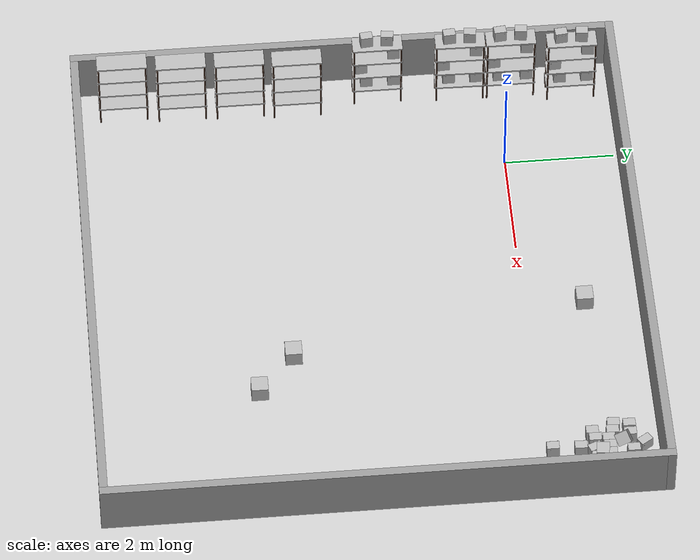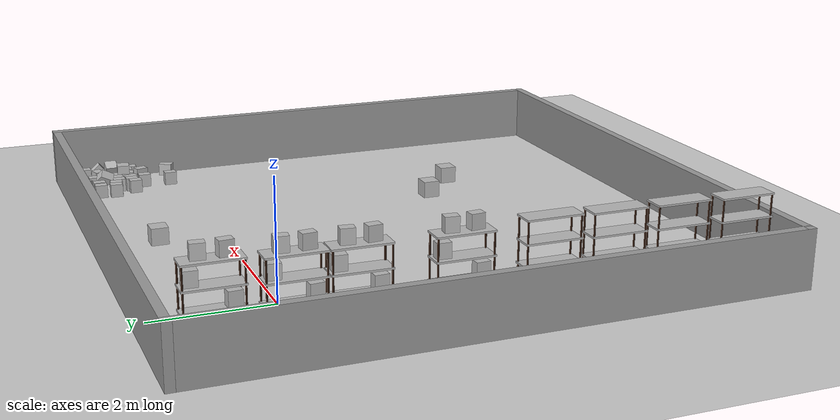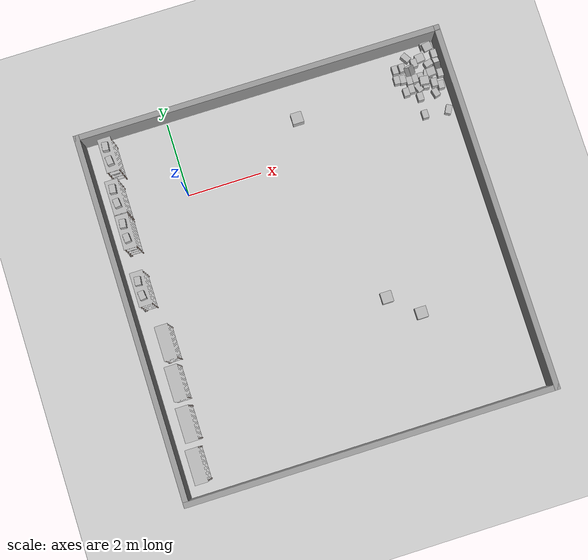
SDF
<sdf version="1.7">
 <world name="default">
  <light name="sun" type="directional">
   <pose>0 0 10 0 -0 0</pose>
   <diffuse>0.8 0.8 0.8 1</diffuse>
   <specular>0.2 0.2 0.2 1</specular>
   <attenuation>
    <range>1000</range>
    <constant>0.9</constant>
    <linear>0.01</linear>
    <quadratic>0.001</quadratic>
   </attenuation>
   <direction>-0.5 0.1 -0.9</direction>
   <spot><inner_angle>0</inner_angle><outer_angle>0</outer_angle><falloff>0</falloff></spot>
  </light>
  <model name="ground_plane">
   <static>1</static>
   <link name="link">
    <collision name="collision">
     <geometry><plane><normal>0 0 1</normal><size>100 100</size></plane></geometry>
     <surface><friction><ode><mu>100</mu><mu2>50</mu2></ode></friction></surface>
    </collision>
    <visual name="visual">
     <cast_shadows>0</cast_shadows>
     <geometry><plane><normal>0 0 1</normal><size>100 100</size></plane></geometry>
     <material>
      <script><uri>file://media/materials/scripts/gazebo.material</uri><name>Gazebo/Grey</name></script>
     </material>
    </visual>
   </link>
  </model>
  <gravity>0 0 -9.8</gravity>
  <magnetic_field>6e-06 2.3e-05 -4.2e-05</magnetic_field>
  <atmosphere type="adiabatic"/>
  <physics type="ode">
   <max_step_size>0.001</max_step_size>
   <real_time_factor>1</real_time_factor>
   <real_time_update_rate>1000</real_time_update_rate>
  </physics>
  <scene><ambient>0.4 0.4 0.4 1</ambient><background>0.7 0.7 0.7 1</background><shadows>1</shadows></scene>
  <audio><device>default</device></audio>
  <spherical_coordinates>
   <surface_model>EARTH_WGS84</surface_model>
   <latitude_deg>0</latitude_deg>
   <longitude_deg>0</longitude_deg>
   <elevation>0</elevation>
   <heading_deg>0</heading_deg>
  </spherical_coordinates>
  <model name="EmptyRoom">
   <pose>2.61415 -2.78471 0 0 -0 0</pose>
   <link name="Wall_1">
    <collision name="Wall_1_Collision">
     <geometry><box><size>10 0.15 1</size></box></geometry>
     <pose>0 0 0.5 0 -0 0</pose>
    </collision>
    <visual name="Wall_1_Visual">
     <pose>0 0 0.5 0 -0 0</pose>
     <geometry><box><size>10 0.15 1</size></box></geometry>
     <material>
      <script><uri>file://media/materials/scripts/gazebo.material</uri><name>Gazebo/Grey</name></script>
      <ambient>1 1 1 1</ambient>
     </material>
     <meta><layer>0</layer></meta>
    </visual>
    <pose>-4.925 0 0 0 -0 -1.5708</pose>
   </link>
   <link name="Wall_2">
    <collision name="Wall_2_Collision">
     <geometry><box><size>10 0.15 1</size></box></geometry>
     <pose>0 0 0.5 0 -0 0</pose>
    </collision>
    <visual name="Wall_2_Visual">
     <pose>0 0 0.5 0 -0 0</pose>
     <geometry><box><size>10 0.15 1</size></box></geometry>
     <material>
      <script><uri>file://media/materials/scripts/gazebo.material</uri><name>Gazebo/Grey</name></script>
      <ambient>1 1 1 1</ambient>
     </material>
     <meta><layer>0</layer></meta>
    </visual>
    <pose>-0 -4.925 0 0 -0 0</pose>
   </link>
   <link name="Wall_3">
    <collision name="Wall_3_Collision">
     <geometry><box><size>10 0.15 1</size></box></geometry>
     <pose>0 0 0.5 0 -0 0</pose>
    </collision>
    <visual name="Wall_3_Visual">
     <pose>0 0 0.5 0 -0 0</pose>
     <geometry><box><size>10 0.15 1</size></box></geometry>
     <material>
      <script><uri>file://media/materials/scripts/gazebo.material</uri><name>Gazebo/Grey</name></script>
      <ambient>1 1 1 1</ambient>
     </material>
     <meta><layer>0</layer></meta>
    </visual>
    <pose>4.925 0 0 0 -0 1.5708</pose>
   </link>
   <link name="Wall_4">
    <collision name="Wall_4_Collision">
     <geometry><box><size>10 0.15 1</size></box></geometry>
     <pose>0 0 0.5 0 -0 0</pose>
    </collision>
    <visual name="Wall_4_Visual">
     <pose>0 0 0.5 0 -0 0</pose>
     <geometry><box><size>10 0.15 1</size></box></geometry>
     <material>
      <script><uri>file://media/materials/scripts/gazebo.material</uri><name>Gazebo/Grey</name></script>
      <ambient>1 1 1 1</ambient>
     </material>
     <meta><layer>0</layer></meta>
    </visual>
    <pose>-0 4.925 0 0 -0 3.14159</pose>
   </link>
   <static>1</static>
  </model>
  <model name="box">
   <link name="link">
    <inertial>
     <inertia>
      <ixx>0.00220983</ixx>
      <ixy>0</ixy>
      <ixz>0</ixz>
      <iyy>0.00128087</iyy>
      <iyz>0</iyz>
      <izz>0.00244903</izz>
     </inertia>
     <mass>0.01</mass>
    </inertial>
    <visual name="visual1">
     <cast_shadows>0</cast_shadows>
     <geometry><mesh><uri>model://box/meshes/box.dae</uri></mesh></geometry>
     <material>
      <shader type="pixel"><normal_map>__default__</normal_map></shader>
      <emissive>0 0 0 1</emissive>
     </material>
     <pose>0 0 -0.12 0 -0 0</pose>
    </visual>
    <collision name="collision_0">
     <geometry><box><size>0.16 0.22 0.24</size></box></geometry>
     <surface>
      <friction>
       <ode><mu>1</mu><mu2>1</mu2><fdir1>0 0 0</fdir1><slip1>0</slip1><slip2>0</slip2></ode>
       <torsional>
        <coefficient>1</coefficient>
        <patch_radius>0</patch_radius>
        <surface_radius>0</surface_radius>
        <use_patch_radius>1</use_patch_radius>
        <ode><slip>0</slip></ode>
       </torsional>
      </friction>
      <bounce><restitution_coefficient>0</restitution_coefficient><threshold>1e+06</threshold></bounce>
      <contact>
       <collide_without_contact>0</collide_without_contact>
       <collide_without_contact_bitmask>1</collide_without_contact_bitmask>
       <collide_bitmask>1</collide_bitmask>
       <ode>
        <soft_cfm>0</soft_cfm>
        <soft_erp>0.2</soft_erp>
        <kp>1e+13</kp>
        <kd>1</kd>
        <max_vel>0.01</max_vel>
        <min_depth>0</min_depth>
       </ode>
       <bullet>
        <split_impulse>1</split_impulse>
        <split_impulse_penetration_threshold>-0.01</split_impulse_penetration_threshold>
        <soft_cfm>0</soft_cfm>
        <soft_erp>0.2</soft_erp>
        <kp>1e+13</kp>
        <kd>1</kd>
       </bullet>
      </contact>
     </surface>
    </collision>
   </link>
   <static>0</static>
   <pose>6.6949 1.18742 0.119988 -1.3e-05 -4e-06 -0.023776</pose>
  </model>
  <model name="box_0">
   <link name="link">
    <inertial>
     <inertia>
      <ixx>0.00220983</ixx>
      <ixy>0</ixy>
      <ixz>0</ixz>
      <iyy>0.00128087</iyy>
      <iyz>0</iyz>
      <izz>0.00244903</izz>
     </inertia>
     <mass>0.01</mass>
    </inertial>
    <visual name="visual1">
     <cast_shadows>0</cast_shadows>
     <geometry><mesh><uri>model://box/meshes/box.dae</uri></mesh></geometry>
     <material>
      <shader type="pixel"><normal_map>__default__</normal_map></shader>
      <emissive>0 0 0 1</emissive>
     </material>
     <pose>0 0 -0.12 0 -0 0</pose>
    </visual>
    <collision name="collision_0">
     <geometry><box><size>0.16 0.22 0.24</size></box></geometry>
     <surface>
      <friction>
       <ode><mu>1</mu><mu2>1</mu2><fdir1>0 0 0</fdir1><slip1>0</slip1><slip2>0</slip2></ode>
       <torsional>
        <coefficient>1</coefficient>
        <patch_radius>0</patch_radius>
        <surface_radius>0</surface_radius>
        <use_patch_radius>1</use_patch_radius>
        <ode><slip>0</slip></ode>
       </torsional>
      </friction>
      <bounce><restitution_coefficient>0</restitution_coefficient><threshold>1e+06</threshold></bounce>
      <contact>
       <collide_without_contact>0</collide_without_contact>
       <collide_without_contact_bitmask>1</collide_without_contact_bitmask>
       <collide_bitmask>1</collide_bitmask>
       <ode>
        <soft_cfm>0</soft_cfm>
        <soft_erp>0.2</soft_erp>
        <kp>1e+13</kp>
        <kd>1</kd>
        <max_vel>0.01</max_vel>
        <min_depth>0</min_depth>
       </ode>
       <bullet>
        <split_impulse>1</split_impulse>
        <split_impulse_penetration_threshold>-0.01</split_impulse_penetration_threshold>
        <soft_cfm>0</soft_cfm>
        <soft_erp>0.2</soft_erp>
        <kp>1e+13</kp>
        <kd>1</kd>
       </bullet>
      </contact>
     </surface>
    </collision>
   </link>
   <static>0</static>
   <pose>7.1612 1.4756 0.12 0 0 -1.30545</pose>
  </model>
  <model name="box_1">
   <link name="link">
    <inertial>
     <inertia>
      <ixx>0.00220983</ixx>
      <ixy>0</ixy>
      <ixz>0</ixz>
      <iyy>0.00128087</iyy>
      <iyz>0</iyz>
      <izz>0.00244903</izz>
     </inertia>
     <mass>0.01</mass>
    </inertial>
    <visual name="visual1">
     <cast_shadows>0</cast_shadows>
     <geometry><mesh><uri>model://box/meshes/box.dae</uri></mesh></geometry>
     <material>
      <shader type="pixel"><normal_map>__default__</normal_map></shader>
      <emissive>0 0 0 1</emissive>
     </material>
     <pose>0 0 -0.12 0 -0 0</pose>
    </visual>
    <collision name="collision_0">
     <geometry><box><size>0.16 0.22 0.24</size></box></geometry>
     <surface>
      <friction>
       <ode><mu>1</mu><mu2>1</mu2><fdir1>0 0 0</fdir1><slip1>0</slip1><slip2>0</slip2></ode>
       <torsional>
        <coefficient>1</coefficient>
        <patch_radius>0</patch_radius>
        <surface_radius>0</surface_radius>
        <use_patch_radius>1</use_patch_radius>
        <ode><slip>0</slip></ode>
       </torsional>
      </friction>
      <bounce><restitution_coefficient>0</restitution_coefficient><threshold>1e+06</threshold></bounce>
      <contact>
       <collide_without_contact>0</collide_without_contact>
       <collide_without_contact_bitmask>1</collide_without_contact_bitmask>
       <collide_bitmask>1</collide_bitmask>
       <ode>
        <soft_cfm>0</soft_cfm>
        <soft_erp>0.2</soft_erp>
        <kp>1e+13</kp>
        <kd>1</kd>
        <max_vel>0.01</max_vel>
        <min_depth>0</min_depth>
       </ode>
       <bullet>
        <split_impulse>1</split_impulse>
        <split_impulse_penetration_threshold>-0.01</split_impulse_penetration_threshold>
        <soft_cfm>0</soft_cfm>
        <soft_erp>0.2</soft_erp>
        <kp>1e+13</kp>
        <kd>1</kd>
       </bullet>
      </contact>
     </surface>
    </collision>
   </link>
   <static>0</static>
   <pose>7.38401 1.68891 0.1183 -1.1e-05 -7e-05 0.00035</pose>
  </model>
  <model name="box_2">
   <link name="link">
    <inertial>
     <inertia>
      <ixx>0.00220983</ixx>
      <ixy>0</ixy>
      <ixz>0</ixz>
      <iyy>0.00128087</iyy>
      <iyz>0</iyz>
      <izz>0.00244903</izz>
     </inertia>
     <mass>0.01</mass>
    </inertial>
    <visual name="visual1">
     <cast_shadows>0</cast_shadows>
     <geometry><mesh><uri>model://box/meshes/box.dae</uri></mesh></geometry>
     <material>
      <shader type="pixel"><normal_map>__default__</normal_map></shader>
      <emissive>0 0 0 1</emissive>
     </material>
     <pose>0 0 -0.12 0 -0 0</pose>
    </visual>
    <collision name="collision_0">
     <geometry><box><size>0.16 0.22 0.24</size></box></geometry>
     <surface>
      <friction>
       <ode><mu>1</mu><mu2>1</mu2><fdir1>0 0 0</fdir1><slip1>0</slip1><slip2>0</slip2></ode>
       <torsional>
        <coefficient>1</coefficient>
        <patch_radius>0</patch_radius>
        <surface_radius>0</surface_radius>
        <use_patch_radius>1</use_patch_radius>
        <ode><slip>0</slip></ode>
       </torsional>
      </friction>
      <bounce><restitution_coefficient>0</restitution_coefficient><threshold>1e+06</threshold></bounce>
      <contact>
       <collide_without_contact>0</collide_without_contact>
       <collide_without_contact_bitmask>1</collide_without_contact_bitmask>
       <collide_bitmask>1</collide_bitmask>
       <ode>
        <soft_cfm>0</soft_cfm>
        <soft_erp>0.2</soft_erp>
        <kp>1e+13</kp>
        <kd>1</kd>
        <max_vel>0.01</max_vel>
        <min_depth>0</min_depth>
       </ode>
       <bullet>
        <split_impulse>1</split_impulse>
        <split_impulse_penetration_threshold>-0.01</split_impulse_penetration_threshold>
        <soft_cfm>0</soft_cfm>
        <soft_erp>0.2</soft_erp>
        <kp>1e+13</kp>
        <kd>1</kd>
       </bullet>
      </contact>
     </surface>
    </collision>
   </link>
   <static>0</static>
   <pose>6.99735 1.70085 0.08 2.78611 1.57079 2.90216</pose>
  </model>
  <model name="box_3">
   <link name="link">
    <inertial>
     <inertia>
      <ixx>0.00220983</ixx>
      <ixy>0</ixy>
      <ixz>0</ixz>
      <iyy>0.00128087</iyy>
      <iyz>0</iyz>
      <izz>0.00244903</izz>
     </inertia>
     <mass>0.01</mass>
    </inertial>
    <visual name="visual1">
     <cast_shadows>0</cast_shadows>
     <geometry><mesh><uri>model://box/meshes/box.dae</uri></mesh></geometry>
     <material>
      <shader type="pixel"><normal_map>__default__</normal_map></shader>
      <emissive>0 0 0 1</emissive>
     </material>
     <pose>0 0 -0.12 0 -0 0</pose>
    </visual>
    <collision name="collision_0">
     <geometry><box><size>0.16 0.22 0.24</size></box></geometry>
     <surface>
      <friction>
       <ode><mu>1</mu><mu2>1</mu2><fdir1>0 0 0</fdir1><slip1>0</slip1><slip2>0</slip2></ode>
       <torsional>
        <coefficient>1</coefficient>
        <patch_radius>0</patch_radius>
        <surface_radius>0</surface_radius>
        <use_patch_radius>1</use_patch_radius>
        <ode><slip>0</slip></ode>
       </torsional>
      </friction>
      <bounce><restitution_coefficient>0</restitution_coefficient><threshold>1e+06</threshold></bounce>
      <contact>
       <collide_without_contact>0</collide_without_contact>
       <collide_without_contact_bitmask>1</collide_without_contact_bitmask>
       <collide_bitmask>1</collide_bitmask>
       <ode>
        <soft_cfm>0</soft_cfm>
        <soft_erp>0.2</soft_erp>
        <kp>1e+13</kp>
        <kd>1</kd>
        <max_vel>0.01</max_vel>
        <min_depth>0</min_depth>
       </ode>
       <bullet>
        <split_impulse>1</split_impulse>
        <split_impulse_penetration_threshold>-0.01</split_impulse_penetration_threshold>
        <soft_cfm>0</soft_cfm>
        <soft_erp>0.2</soft_erp>
        <kp>1e+13</kp>
        <kd>1</kd>
       </bullet>
      </contact>
     </surface>
    </collision>
   </link>
   <static>0</static>
   <pose>7.16624 1.21663 0.27562 -0.000355 1.22733 -0.000252</pose>
  </model>
  <model name="box_4">
   <link name="link">
    <inertial>
     <inertia>
      <ixx>0.00220983</ixx>
      <ixy>0</ixy>
      <ixz>0</ixz>
      <iyy>0.00128087</iyy>
      <iyz>0</iyz>
      <izz>0.00244903</izz>
     </inertia>
     <mass>0.01</mass>
    </inertial>
    <visual name="visual1">
     <cast_shadows>0</cast_shadows>
     <geometry><mesh><uri>model://box/meshes/box.dae</uri></mesh></geometry>
     <material>
      <shader type="pixel"><normal_map>__default__</normal_map></shader>
      <emissive>0 0 0 1</emissive>
     </material>
     <pose>0 0 -0.12 0 -0 0</pose>
    </visual>
    <collision name="collision_0">
     <geometry><box><size>0.16 0.22 0.24</size></box></geometry>
     <surface>
      <friction>
       <ode><mu>1</mu><mu2>1</mu2><fdir1>0 0 0</fdir1><slip1>0</slip1><slip2>0</slip2></ode>
       <torsional>
        <coefficient>1</coefficient>
        <patch_radius>0</patch_radius>
        <surface_radius>0</surface_radius>
        <use_patch_radius>1</use_patch_radius>
        <ode><slip>0</slip></ode>
       </torsional>
      </friction>
      <bounce><restitution_coefficient>0</restitution_coefficient><threshold>1e+06</threshold></bounce>
      <contact>
       <collide_without_contact>0</collide_without_contact>
       <collide_without_contact_bitmask>1</collide_without_contact_bitmask>
       <collide_bitmask>1</collide_bitmask>
       <ode>
        <soft_cfm>0</soft_cfm>
        <soft_erp>0.2</soft_erp>
        <kp>1e+13</kp>
        <kd>1</kd>
        <max_vel>0.01</max_vel>
        <min_depth>0</min_depth>
       </ode>
       <bullet>
        <split_impulse>1</split_impulse>
        <split_impulse_penetration_threshold>-0.01</split_impulse_penetration_threshold>
        <soft_cfm>0</soft_cfm>
        <soft_erp>0.2</soft_erp>
        <kp>1e+13</kp>
        <kd>1</kd>
       </bullet>
      </contact>
     </surface>
    </collision>
   </link>
   <static>0</static>
   <pose>6.3618 0.900243 0.12 0 3e-06 0.003147</pose>
  </model>
  <model name="box_5">
   <link name="link">
    <inertial>
     <inertia>
      <ixx>0.00220983</ixx>
      <ixy>0</ixy>
      <ixz>0</ixz>
      <iyy>0.00128087</iyy>
      <iyz>0</iyz>
      <izz>0.00244903</izz>
     </inertia>
     <mass>0.01</mass>
    </inertial>
    <visual name="visual1">
     <cast_shadows>0</cast_shadows>
     <geometry><mesh><uri>model://box/meshes/box.dae</uri></mesh></geometry>
     <material>
      <shader type="pixel"><normal_map>__default__</normal_map></shader>
      <emissive>0 0 0 1</emissive>
     </material>
     <pose>0 0 -0.12 0 -0 0</pose>
    </visual>
    <collision name="collision_0">
     <geometry><box><size>0.16 0.22 0.24</size></box></geometry>
     <surface>
      <friction>
       <ode><mu>1</mu><mu2>1</mu2><fdir1>0 0 0</fdir1><slip1>0</slip1><slip2>0</slip2></ode>
       <torsional>
        <coefficient>1</coefficient>
        <patch_radius>0</patch_radius>
        <surface_radius>0</surface_radius>
        <use_patch_radius>1</use_patch_radius>
        <ode><slip>0</slip></ode>
       </torsional>
      </friction>
      <bounce><restitution_coefficient>0</restitution_coefficient><threshold>1e+06</threshold></bounce>
      <contact>
       <collide_without_contact>0</collide_without_contact>
       <collide_without_contact_bitmask>1</collide_without_contact_bitmask>
       <collide_bitmask>1</collide_bitmask>
       <ode>
        <soft_cfm>0</soft_cfm>
        <soft_erp>0.2</soft_erp>
        <kp>1e+13</kp>
        <kd>1</kd>
        <max_vel>0.01</max_vel>
        <min_depth>0</min_depth>
       </ode>
       <bullet>
        <split_impulse>1</split_impulse>
        <split_impulse_penetration_threshold>-0.01</split_impulse_penetration_threshold>
        <soft_cfm>0</soft_cfm>
        <soft_erp>0.2</soft_erp>
        <kp>1e+13</kp>
        <kd>1</kd>
       </bullet>
      </contact>
     </surface>
    </collision>
   </link>
   <static>0</static>
   <pose>7.31334 0.826569 0.12 0 -0 -0.019346</pose>
  </model>
  <model name="box_6">
   <link name="link">
    <inertial>
     <inertia>
      <ixx>0.00220983</ixx>
      <ixy>0</ixy>
      <ixz>0</ixz>
      <iyy>0.00128087</iyy>
      <iyz>0</iyz>
      <izz>0.00244903</izz>
     </inertia>
     <mass>0.01</mass>
    </inertial>
    <visual name="visual1">
     <cast_shadows>0</cast_shadows>
     <geometry><mesh><uri>model://box/meshes/box.dae</uri></mesh></geometry>
     <material>
      <shader type="pixel"><normal_map>__default__</normal_map></shader>
      <emissive>0 0 0 1</emissive>
     </material>
     <pose>0 0 -0.12 0 -0 0</pose>
    </visual>
    <collision name="collision_0">
     <geometry><box><size>0.16 0.22 0.24</size></box></geometry>
     <surface>
      <friction>
       <ode><mu>1</mu><mu2>1</mu2><fdir1>0 0 0</fdir1><slip1>0</slip1><slip2>0</slip2></ode>
       <torsional>
        <coefficient>1</coefficient>
        <patch_radius>0</patch_radius>
        <surface_radius>0</surface_radius>
        <use_patch_radius>1</use_patch_radius>
        <ode><slip>0</slip></ode>
       </torsional>
      </friction>
      <bounce><restitution_coefficient>0</restitution_coefficient><threshold>1e+06</threshold></bounce>
      <contact>
       <collide_without_contact>0</collide_without_contact>
       <collide_without_contact_bitmask>1</collide_without_contact_bitmask>
       <collide_bitmask>1</collide_bitmask>
       <ode>
        <soft_cfm>0</soft_cfm>
        <soft_erp>0.2</soft_erp>
        <kp>1e+13</kp>
        <kd>1</kd>
        <max_vel>0.01</max_vel>
        <min_depth>0</min_depth>
       </ode>
       <bullet>
        <split_impulse>1</split_impulse>
        <split_impulse_penetration_threshold>-0.01</split_impulse_penetration_threshold>
        <soft_cfm>0</soft_cfm>
        <soft_erp>0.2</soft_erp>
        <kp>1e+13</kp>
        <kd>1</kd>
       </bullet>
      </contact>
     </surface>
    </collision>
   </link>
   <static>0</static>
   <pose>6.52175 0.940974 0.12 0 -0 0.004081</pose>
  </model>
  <model name="box_7">
   <link name="link">
    <inertial>
     <inertia>
      <ixx>0.00220983</ixx>
      <ixy>0</ixy>
      <ixz>0</ixz>
      <iyy>0.00128087</iyy>
      <iyz>0</iyz>
      <izz>0.00244903</izz>
     </inertia>
     <mass>0.01</mass>
    </inertial>
    <visual name="visual1">
     <cast_shadows>0</cast_shadows>
     <geometry><mesh><uri>model://box/meshes/box.dae</uri></mesh></geometry>
     <material>
      <shader type="pixel"><normal_map>__default__</normal_map></shader>
      <emissive>0 0 0 1</emissive>
     </material>
     <pose>0 0 -0.12 0 -0 0</pose>
    </visual>
    <collision name="collision_0">
     <geometry><box><size>0.16 0.22 0.24</size></box></geometry>
     <surface>
      <friction>
       <ode><mu>1</mu><mu2>1</mu2><fdir1>0 0 0</fdir1><slip1>0</slip1><slip2>0</slip2></ode>
       <torsional>
        <coefficient>1</coefficient>
        <patch_radius>0</patch_radius>
        <surface_radius>0</surface_radius>
        <use_patch_radius>1</use_patch_radius>
        <ode><slip>0</slip></ode>
       </torsional>
      </friction>
      <bounce><restitution_coefficient>0</restitution_coefficient><threshold>1e+06</threshold></bounce>
      <contact>
       <collide_without_contact>0</collide_without_contact>
       <collide_without_contact_bitmask>1</collide_without_contact_bitmask>
       <collide_bitmask>1</collide_bitmask>
       <ode>
        <soft_cfm>0</soft_cfm>
        <soft_erp>0.2</soft_erp>
        <kp>1e+13</kp>
        <kd>1</kd>
        <max_vel>0.01</max_vel>
        <min_depth>0</min_depth>
       </ode>
       <bullet>
        <split_impulse>1</split_impulse>
        <split_impulse_penetration_threshold>-0.01</split_impulse_penetration_threshold>
        <soft_cfm>0</soft_cfm>
        <soft_erp>0.2</soft_erp>
        <kp>1e+13</kp>
        <kd>1</kd>
       </bullet>
      </contact>
     </surface>
    </collision>
   </link>
   <static>0</static>
   <pose>6.53397 1.17825 0.12 0 0 -0.02989</pose>
  </model>
  <model name="rack">
   <link name="link">
    <inertial>
     <mass>0.1</mass>
     <inertia><ixx>0.01857</ixx><ixy>0</ixy><ixz>0</ixz><iyy>0.015598</iyy><iyz>0</iyz><izz>0.00305</izz></inertia>
    </inertial>
    <visual name="visual1">
     <cast_shadows>0</cast_shadows>
     <geometry><mesh><uri>model://rack/meshes/rack.dae</uri></mesh></geometry>
     <material>
      <shader type="pixel"><normal_map>__default__</normal_map></shader>
      <emissive>0 0 0 1</emissive>
     </material>
    </visual>
    <visual name="visual_2">
     <cast_shadows>0</cast_shadows>
     <geometry><box><size>0.02 0.9 0.31</size></box></geometry>
     <material>
      <lighting>1</lighting>
      <script><uri>file://media/materials/scripts/gazebo.material</uri><name>Gazebo/Grey</name></script>
      <shader type="pixel"><normal_map>__default__</normal_map></shader>
      <ambient>0.3 0.3 0.3 1</ambient>
      <diffuse>0.7 0.7 0.7 1</diffuse>
      <specular>0.01 0.01 0.01 1</specular>
      <emissive>0 0 0 1</emissive>
     </material>
     <pose>-0.185 0 0.22 0 -0 0</pose>
    </visual>
    <collision name="collision_7">
     <pose>0 0 0.36 0 1.57 1.57</pose>
     <geometry><box><size>0.05 0.35 0.91</size></box></geometry>
     <surface>
      <friction>
       <ode><mu>1</mu><mu2>1</mu2><fdir1>0 0 0</fdir1><slip1>0</slip1><slip2>0</slip2></ode>
       <torsional>
        <coefficient>1</coefficient>
        <patch_radius>0</patch_radius>
        <surface_radius>0</surface_radius>
        <use_patch_radius>1</use_patch_radius>
        <ode><slip>0</slip></ode>
       </torsional>
      </friction>
      <bounce><restitution_coefficient>0</restitution_coefficient><threshold>1e+06</threshold></bounce>
      <contact>
       <collide_without_contact>0</collide_without_contact>
       <collide_without_contact_bitmask>1</collide_without_contact_bitmask>
       <collide_bitmask>1</collide_bitmask>
       <ode>
        <soft_cfm>0</soft_cfm>
        <soft_erp>0.2</soft_erp>
        <kp>1e+15</kp>
        <kd>1e+13</kd>
        <max_vel>0.01</max_vel>
        <min_depth>0</min_depth>
       </ode>
       <bullet>
        <split_impulse>1</split_impulse>
        <split_impulse_penetration_threshold>-0.01</split_impulse_penetration_threshold>
        <soft_cfm>0</soft_cfm>
        <soft_erp>0.2</soft_erp>
        <kp>1e+13</kp>
        <kd>1</kd>
       </bullet>
      </contact>
     </surface>
    </collision>
    <collision name="collision_6">
     <pose>0 0 0.725 0 1.57 1.57</pose>
     <geometry><box><size>0.05 0.35 0.91</size></box></geometry>
     <surface>
      <friction>
       <ode><mu>1</mu><mu2>1</mu2><fdir1>0 0 0</fdir1><slip1>0</slip1><slip2>0</slip2></ode>
       <torsional>
        <coefficient>1</coefficient>
        <patch_radius>0</patch_radius>
        <surface_radius>0</surface_radius>
        <use_patch_radius>1</use_patch_radius>
        <ode><slip>0</slip></ode>
       </torsional>
      </friction>
      <bounce><restitution_coefficient>0</restitution_coefficient><threshold>1e+06</threshold></bounce>
      <contact>
       <collide_without_contact>0</collide_without_contact>
       <collide_without_contact_bitmask>1</collide_without_contact_bitmask>
       <collide_bitmask>1</collide_bitmask>
       <ode>
        <soft_cfm>0</soft_cfm>
        <soft_erp>0.2</soft_erp>
        <kp>1e+15</kp>
        <kd>1e+13</kd>
        <max_vel>0.01</max_vel>
        <min_depth>0</min_depth>
       </ode>
       <bullet>
        <split_impulse>1</split_impulse>
        <split_impulse_penetration_threshold>-0.01</split_impulse_penetration_threshold>
        <soft_cfm>0</soft_cfm>
        <soft_erp>0.2</soft_erp>
        <kp>1e+13</kp>
        <kd>1</kd>
       </bullet>
      </contact>
     </surface>
    </collision>
    <collision name="collision_5">
     <pose>0 0 1.09 0 1.57 1.57</pose>
     <geometry><box><size>0.05 0.35 0.91</size></box></geometry>
     <surface>
      <friction>
       <ode><mu>1</mu><mu2>1</mu2><fdir1>0 0 0</fdir1><slip1>0</slip1><slip2>0</slip2></ode>
       <torsional>
        <coefficient>1</coefficient>
        <patch_radius>0</patch_radius>
        <surface_radius>0</surface_radius>
        <use_patch_radius>1</use_patch_radius>
        <ode><slip>0</slip></ode>
       </torsional>
      </friction>
      <bounce><restitution_coefficient>0</restitution_coefficient><threshold>1e+06</threshold></bounce>
      <contact>
       <collide_without_contact>0</collide_without_contact>
       <collide_without_contact_bitmask>1</collide_without_contact_bitmask>
       <collide_bitmask>1</collide_bitmask>
       <ode>
        <soft_cfm>0</soft_cfm>
        <soft_erp>0.2</soft_erp>
        <kp>1e+15</kp>
        <kd>1e+13</kd>
        <max_vel>0.01</max_vel>
        <min_depth>0</min_depth>
       </ode>
       <bullet>
        <split_impulse>1</split_impulse>
        <split_impulse_penetration_threshold>-0.01</split_impulse_penetration_threshold>
        <soft_cfm>0</soft_cfm>
        <soft_erp>0.2</soft_erp>
        <kp>1e+13</kp>
        <kd>1</kd>
       </bullet>
      </contact>
     </surface>
    </collision>
    <collision name="collision_3">
     <pose>0 0 1.455 0 1.57 1.57</pose>
     <geometry><box><size>0.05 0.35 0.91</size></box></geometry>
     <surface>
      <friction>
       <ode><mu>1</mu><mu2>1</mu2><fdir1>0 0 0</fdir1><slip1>0</slip1><slip2>0</slip2></ode>
       <torsional>
        <coefficient>1</coefficient>
        <patch_radius>0</patch_radius>
        <surface_radius>0</surface_radius>
        <use_patch_radius>1</use_patch_radius>
        <ode><slip>0</slip></ode>
       </torsional>
      </friction>
      <bounce><restitution_coefficient>0</restitution_coefficient><threshold>1e+06</threshold></bounce>
      <contact>
       <collide_without_contact>0</collide_without_contact>
       <collide_without_contact_bitmask>1</collide_without_contact_bitmask>
       <collide_bitmask>1</collide_bitmask>
       <ode>
        <soft_cfm>0</soft_cfm>
        <soft_erp>0.2</soft_erp>
        <kp>1e+15</kp>
        <kd>1e+13</kd>
        <max_vel>0.01</max_vel>
        <min_depth>0</min_depth>
       </ode>
       <bullet>
        <split_impulse>1</split_impulse>
        <split_impulse_penetration_threshold>-0.01</split_impulse_penetration_threshold>
        <soft_cfm>0</soft_cfm>
        <soft_erp>0.2</soft_erp>
        <kp>1e+13</kp>
        <kd>1</kd>
       </bullet>
      </contact>
     </surface>
    </collision>
    <collision name="collision_1">
     <pose>0 0.43 0.73 0 -0 1.57</pose>
     <geometry><box><size>0.05 0.36 1.46</size></box></geometry>
     <surface>
      <friction>
       <ode><mu>1</mu><mu2>1</mu2><fdir1>0 0 0</fdir1><slip1>0</slip1><slip2>0</slip2></ode>
       <torsional>
        <coefficient>1</coefficient>
        <patch_radius>0</patch_radius>
        <surface_radius>0</surface_radius>
        <use_patch_radius>1</use_patch_radius>
        <ode><slip>0</slip></ode>
       </torsional>
      </friction>
      <bounce><restitution_coefficient>0</restitution_coefficient><threshold>1e+06</threshold></bounce>
      <contact>
       <collide_without_contact>0</collide_without_contact>
       <collide_without_contact_bitmask>1</collide_without_contact_bitmask>
       <collide_bitmask>1</collide_bitmask>
       <ode>
        <soft_cfm>0</soft_cfm>
        <soft_erp>0.2</soft_erp>
        <kp>1e+15</kp>
        <kd>1e+13</kd>
        <max_vel>0.01</max_vel>
        <min_depth>0</min_depth>
       </ode>
       <bullet>
        <split_impulse>1</split_impulse>
        <split_impulse_penetration_threshold>-0.01</split_impulse_penetration_threshold>
        <soft_cfm>0</soft_cfm>
        <soft_erp>0.2</soft_erp>
        <kp>1e+13</kp>
        <kd>1</kd>
       </bullet>
      </contact>
     </surface>
    </collision>
    <collision name="collision_2">
     <pose>0 -0.43 0.73 0 -0 1.57</pose>
     <geometry><box><size>0.05 0.36 1.46</size></box></geometry>
     <surface>
      <friction>
       <ode><mu>1</mu><mu2>1</mu2><fdir1>0 0 0</fdir1><slip1>0</slip1><slip2>0</slip2></ode>
       <torsional>
        <coefficient>1</coefficient>
        <patch_radius>0</patch_radius>
        <surface_radius>0</surface_radius>
        <use_patch_radius>1</use_patch_radius>
        <ode><slip>0</slip></ode>
       </torsional>
      </friction>
      <bounce><restitution_coefficient>0</restitution_coefficient><threshold>1e+06</threshold></bounce>
      <contact>
       <collide_without_contact>0</collide_without_contact>
       <collide_without_contact_bitmask>1</collide_without_contact_bitmask>
       <collide_bitmask>1</collide_bitmask>
       <ode>
        <soft_cfm>0</soft_cfm>
        <soft_erp>0.2</soft_erp>
        <kp>1e+15</kp>
        <kd>1e+13</kd>
        <max_vel>0.01</max_vel>
        <min_depth>0</min_depth>
       </ode>
       <bullet>
        <split_impulse>1</split_impulse>
        <split_impulse_penetration_threshold>-0.01</split_impulse_penetration_threshold>
        <soft_cfm>0</soft_cfm>
        <soft_erp>0.2</soft_erp>
        <kp>1e+13</kp>
        <kd>1</kd>
       </bullet>
      </contact>
     </surface>
    </collision>
    <collision name="collision">
     <pose>-0.185 0 0.22 0 -0 0</pose>
     <geometry><box><size>0.02 0.9 0.31</size></box></geometry>
     <surface>
      <friction>
       <ode><mu>1</mu><mu2>1</mu2><fdir1>0 0 0</fdir1><slip1>0</slip1><slip2>0</slip2></ode>
       <torsional>
        <coefficient>1</coefficient>
        <patch_radius>0</patch_radius>
        <surface_radius>0</surface_radius>
        <use_patch_radius>1</use_patch_radius>
        <ode><slip>0</slip></ode>
       </torsional>
      </friction>
      <bounce><restitution_coefficient>0</restitution_coefficient><threshold>1e+06</threshold></bounce>
      <contact>
       <collide_without_contact>0</collide_without_contact>
       <collide_without_contact_bitmask>1</collide_without_contact_bitmask>
       <collide_bitmask>1</collide_bitmask>
       <ode>
        <soft_cfm>0</soft_cfm>
        <soft_erp>0.2</soft_erp>
        <kp>1e+15</kp>
        <kd>1e+13</kd>
        <max_vel>0.01</max_vel>
        <min_depth>0</min_depth>
       </ode>
       <bullet>
        <split_impulse>1</split_impulse>
        <split_impulse_penetration_threshold>-0.01</split_impulse_penetration_threshold>
        <soft_cfm>0</soft_cfm>
        <soft_erp>0.2</soft_erp>
        <kp>1e+13</kp>
        <kd>1</kd>
       </bullet>
      </contact>
     </surface>
    </collision>
   </link>
   <static>0</static>
   <pose>-1.73706 -6.85642 -0 0 -0 0</pose>
  </model>
  <model name="rack_0">
   <link name="link">
    <inertial>
     <mass>0.1</mass>
     <inertia><ixx>0.01857</ixx><ixy>0</ixy><ixz>0</ixz><iyy>0.015598</iyy><iyz>0</iyz><izz>0.00305</izz></inertia>
    </inertial>
    <visual name="visual1">
     <cast_shadows>0</cast_shadows>
     <geometry><mesh><uri>model://rack/meshes/rack.dae</uri></mesh></geometry>
     <material>
      <shader type="pixel"><normal_map>__default__</normal_map></shader>
      <emissive>0 0 0 1</emissive>
     </material>
    </visual>
    <visual name="visual_2">
     <cast_shadows>0</cast_shadows>
     <geometry><box><size>0.02 0.9 0.31</size></box></geometry>
     <material>
      <lighting>1</lighting>
      <script><uri>file://media/materials/scripts/gazebo.material</uri><name>Gazebo/Grey</name></script>
      <shader type="pixel"><normal_map>__default__</normal_map></shader>
      <ambient>0.3 0.3 0.3 1</ambient>
      <diffuse>0.7 0.7 0.7 1</diffuse>
      <specular>0.01 0.01 0.01 1</specular>
      <emissive>0 0 0 1</emissive>
     </material>
     <pose>-0.185 0 0.22 0 -0 0</pose>
    </visual>
    <collision name="collision_7">
     <pose>0 0 0.36 0 1.57 1.57</pose>
     <geometry><box><size>0.05 0.35 0.91</size></box></geometry>
     <surface>
      <friction>
       <ode><mu>1</mu><mu2>1</mu2><fdir1>0 0 0</fdir1><slip1>0</slip1><slip2>0</slip2></ode>
       <torsional>
        <coefficient>1</coefficient>
        <patch_radius>0</patch_radius>
        <surface_radius>0</surface_radius>
        <use_patch_radius>1</use_patch_radius>
        <ode><slip>0</slip></ode>
       </torsional>
      </friction>
      <bounce><restitution_coefficient>0</restitution_coefficient><threshold>1e+06</threshold></bounce>
      <contact>
       <collide_without_contact>0</collide_without_contact>
       <collide_without_contact_bitmask>1</collide_without_contact_bitmask>
       <collide_bitmask>1</collide_bitmask>
       <ode>
        <soft_cfm>0</soft_cfm>
        <soft_erp>0.2</soft_erp>
        <kp>1e+15</kp>
        <kd>1e+13</kd>
        <max_vel>0.01</max_vel>
        <min_depth>0</min_depth>
       </ode>
       <bullet>
        <split_impulse>1</split_impulse>
        <split_impulse_penetration_threshold>-0.01</split_impulse_penetration_threshold>
        <soft_cfm>0</soft_cfm>
        <soft_erp>0.2</soft_erp>
        <kp>1e+13</kp>
        <kd>1</kd>
       </bullet>
      </contact>
     </surface>
    </collision>
    <collision name="collision_6">
     <pose>0 0 0.725 0 1.57 1.57</pose>
     <geometry><box><size>0.05 0.35 0.91</size></box></geometry>
     <surface>
      <friction>
       <ode><mu>1</mu><mu2>1</mu2><fdir1>0 0 0</fdir1><slip1>0</slip1><slip2>0</slip2></ode>
       <torsional>
        <coefficient>1</coefficient>
        <patch_radius>0</patch_radius>
        <surface_radius>0</surface_radius>
        <use_patch_radius>1</use_patch_radius>
        <ode><slip>0</slip></ode>
       </torsional>
      </friction>
      <bounce><restitution_coefficient>0</restitution_coefficient><threshold>1e+06</threshold></bounce>
      <contact>
       <collide_without_contact>0</collide_without_contact>
       <collide_without_contact_bitmask>1</collide_without_contact_bitmask>
       <collide_bitmask>1</collide_bitmask>
       <ode>
        <soft_cfm>0</soft_cfm>
        <soft_erp>0.2</soft_erp>
        <kp>1e+15</kp>
        <kd>1e+13</kd>
        <max_vel>0.01</max_vel>
        <min_depth>0</min_depth>
       </ode>
       <bullet>
        <split_impulse>1</split_impulse>
        <split_impulse_penetration_threshold>-0.01</split_impulse_penetration_threshold>
        <soft_cfm>0</soft_cfm>
        <soft_erp>0.2</soft_erp>
        <kp>1e+13</kp>
        <kd>1</kd>
       </bullet>
      </contact>
     </surface>
    </collision>
    <collision name="collision_5">
     <pose>0 0 1.09 0 1.57 1.57</pose>
     <geometry><box><size>0.05 0.35 0.91</size></box></geometry>
     <surface>
      <friction>
       <ode><mu>1</mu><mu2>1</mu2><fdir1>0 0 0</fdir1><slip1>0</slip1><slip2>0</slip2></ode>
       <torsional>
        <coefficient>1</coefficient>
        <patch_radius>0</patch_radius>
        <surface_radius>0</surface_radius>
        <use_patch_radius>1</use_patch_radius>
        <ode><slip>0</slip></ode>
       </torsional>
      </friction>
      <bounce><restitution_coefficient>0</restitution_coefficient><threshold>1e+06</threshold></bounce>
      <contact>
       <collide_without_contact>0</collide_without_contact>
       <collide_without_contact_bitmask>1</collide_without_contact_bitmask>
       <collide_bitmask>1</collide_bitmask>
       <ode>
        <soft_cfm>0</soft_cfm>
        <soft_erp>0.2</soft_erp>
        <kp>1e+15</kp>
        <kd>1e+13</kd>
        <max_vel>0.01</max_vel>
        <min_depth>0</min_depth>
       </ode>
       <bullet>
        <split_impulse>1</split_impulse>
        <split_impulse_penetration_threshold>-0.01</split_impulse_penetration_threshold>
        <soft_cfm>0</soft_cfm>
        <soft_erp>0.2</soft_erp>
        <kp>1e+13</kp>
        <kd>1</kd>
       </bullet>
      </contact>
     </surface>
    </collision>
    <collision name="collision_3">
     <pose>0 0 1.455 0 1.57 1.57</pose>
     <geometry><box><size>0.05 0.35 0.91</size></box></geometry>
     <surface>
      <friction>
       <ode><mu>1</mu><mu2>1</mu2><fdir1>0 0 0</fdir1><slip1>0</slip1><slip2>0</slip2></ode>
       <torsional>
        <coefficient>1</coefficient>
        <patch_radius>0</patch_radius>
        <surface_radius>0</surface_radius>
        <use_patch_radius>1</use_patch_radius>
        <ode><slip>0</slip></ode>
       </torsional>
      </friction>
      <bounce><restitution_coefficient>0</restitution_coefficient><threshold>1e+06</threshold></bounce>
      <contact>
       <collide_without_contact>0</collide_without_contact>
       <collide_without_contact_bitmask>1</collide_without_contact_bitmask>
       <collide_bitmask>1</collide_bitmask>
       <ode>
        <soft_cfm>0</soft_cfm>
        <soft_erp>0.2</soft_erp>
        <kp>1e+15</kp>
        <kd>1e+13</kd>
        <max_vel>0.01</max_vel>
        <min_depth>0</min_depth>
       </ode>
       <bullet>
        <split_impulse>1</split_impulse>
        <split_impulse_penetration_threshold>-0.01</split_impulse_penetration_threshold>
        <soft_cfm>0</soft_cfm>
        <soft_erp>0.2</soft_erp>
        <kp>1e+13</kp>
        <kd>1</kd>
       </bullet>
      </contact>
     </surface>
    </collision>
    <collision name="collision_1">
     <pose>0 0.43 0.73 0 -0 1.57</pose>
     <geometry><box><size>0.05 0.36 1.46</size></box></geometry>
     <surface>
      <friction>
       <ode><mu>1</mu><mu2>1</mu2><fdir1>0 0 0</fdir1><slip1>0</slip1><slip2>0</slip2></ode>
       <torsional>
        <coefficient>1</coefficient>
        <patch_radius>0</patch_radius>
        <surface_radius>0</surface_radius>
        <use_patch_radius>1</use_patch_radius>
        <ode><slip>0</slip></ode>
       </torsional>
      </friction>
      <bounce><restitution_coefficient>0</restitution_coefficient><threshold>1e+06</threshold></bounce>
      <contact>
       <collide_without_contact>0</collide_without_contact>
       <collide_without_contact_bitmask>1</collide_without_contact_bitmask>
       <collide_bitmask>1</collide_bitmask>
       <ode>
        <soft_cfm>0</soft_cfm>
        <soft_erp>0.2</soft_erp>
        <kp>1e+15</kp>
        <kd>1e+13</kd>
        <max_vel>0.01</max_vel>
        <min_depth>0</min_depth>
       </ode>
       <bullet>
        <split_impulse>1</split_impulse>
        <split_impulse_penetration_threshold>-0.01</split_impulse_penetration_threshold>
        <soft_cfm>0</soft_cfm>
        <soft_erp>0.2</soft_erp>
        <kp>1e+13</kp>
        <kd>1</kd>
       </bullet>
      </contact>
     </surface>
    </collision>
    <collision name="collision_2">
     <pose>0 -0.43 0.73 0 -0 1.57</pose>
     <geometry><box><size>0.05 0.36 1.46</size></box></geometry>
     <surface>
      <friction>
       <ode><mu>1</mu><mu2>1</mu2><fdir1>0 0 0</fdir1><slip1>0</slip1><slip2>0</slip2></ode>
       <torsional>
        <coefficient>1</coefficient>
        <patch_radius>0</patch_radius>
        <surface_radius>0</surface_radius>
        <use_patch_radius>1</use_patch_radius>
        <ode><slip>0</slip></ode>
       </torsional>
      </friction>
      <bounce><restitution_coefficient>0</restitution_coefficient><threshold>1e+06</threshold></bounce>
      <contact>
       <collide_without_contact>0</collide_without_contact>
       <collide_without_contact_bitmask>1</collide_without_contact_bitmask>
       <collide_bitmask>1</collide_bitmask>
       <ode>
        <soft_cfm>0</soft_cfm>
        <soft_erp>0.2</soft_erp>
        <kp>1e+15</kp>
        <kd>1e+13</kd>
        <max_vel>0.01</max_vel>
        <min_depth>0</min_depth>
       </ode>
       <bullet>
        <split_impulse>1</split_impulse>
        <split_impulse_penetration_threshold>-0.01</split_impulse_penetration_threshold>
        <soft_cfm>0</soft_cfm>
        <soft_erp>0.2</soft_erp>
        <kp>1e+13</kp>
        <kd>1</kd>
       </bullet>
      </contact>
     </surface>
    </collision>
    <collision name="collision">
     <pose>-0.185 0 0.22 0 -0 0</pose>
     <geometry><box><size>0.02 0.9 0.31</size></box></geometry>
     <surface>
      <friction>
       <ode><mu>1</mu><mu2>1</mu2><fdir1>0 0 0</fdir1><slip1>0</slip1><slip2>0</slip2></ode>
       <torsional>
        <coefficient>1</coefficient>
        <patch_radius>0</patch_radius>
        <surface_radius>0</surface_radius>
        <use_patch_radius>1</use_patch_radius>
        <ode><slip>0</slip></ode>
       </torsional>
      </friction>
      <bounce><restitution_coefficient>0</restitution_coefficient><threshold>1e+06</threshold></bounce>
      <contact>
       <collide_without_contact>0</collide_without_contact>
       <collide_without_contact_bitmask>1</collide_without_contact_bitmask>
       <collide_bitmask>1</collide_bitmask>
       <ode>
        <soft_cfm>0</soft_cfm>
        <soft_erp>0.2</soft_erp>
        <kp>1e+15</kp>
        <kd>1e+13</kd>
        <max_vel>0.01</max_vel>
        <min_depth>0</min_depth>
       </ode>
       <bullet>
        <split_impulse>1</split_impulse>
        <split_impulse_penetration_threshold>-0.01</split_impulse_penetration_threshold>
        <soft_cfm>0</soft_cfm>
        <soft_erp>0.2</soft_erp>
        <kp>1e+13</kp>
        <kd>1</kd>
       </bullet>
      </contact>
     </surface>
    </collision>
   </link>
   <static>0</static>
   <pose>-1.66529 -5.78704 -0 0 -0 0</pose>
  </model>
  <model name="rack_1">
   <link name="link">
    <inertial>
     <mass>0.1</mass>
     <inertia><ixx>0.01857</ixx><ixy>0</ixy><ixz>0</ixz><iyy>0.015598</iyy><iyz>0</iyz><izz>0.00305</izz></inertia>
    </inertial>
    <visual name="visual1">
     <cast_shadows>0</cast_shadows>
     <geometry><mesh><uri>model://rack/meshes/rack.dae</uri></mesh></geometry>
     <material>
      <shader type="pixel"><normal_map>__default__</normal_map></shader>
      <emissive>0 0 0 1</emissive>
     </material>
    </visual>
    <visual name="visual_2">
     <cast_shadows>0</cast_shadows>
     <geometry><box><size>0.02 0.9 0.31</size></box></geometry>
     <material>
      <lighting>1</lighting>
      <script><uri>file://media/materials/scripts/gazebo.material</uri><name>Gazebo/Grey</name></script>
      <shader type="pixel"><normal_map>__default__</normal_map></shader>
      <ambient>0.3 0.3 0.3 1</ambient>
      <diffuse>0.7 0.7 0.7 1</diffuse>
      <specular>0.01 0.01 0.01 1</specular>
      <emissive>0 0 0 1</emissive>
     </material>
     <pose>-0.185 0 0.22 0 -0 0</pose>
    </visual>
    <collision name="collision_7">
     <pose>0 0 0.36 0 1.57 1.57</pose>
     <geometry><box><size>0.05 0.35 0.91</size></box></geometry>
     <surface>
      <friction>
       <ode><mu>1</mu><mu2>1</mu2><fdir1>0 0 0</fdir1><slip1>0</slip1><slip2>0</slip2></ode>
       <torsional>
        <coefficient>1</coefficient>
        <patch_radius>0</patch_radius>
        <surface_radius>0</surface_radius>
        <use_patch_radius>1</use_patch_radius>
        <ode><slip>0</slip></ode>
       </torsional>
      </friction>
      <bounce><restitution_coefficient>0</restitution_coefficient><threshold>1e+06</threshold></bounce>
      <contact>
       <collide_without_contact>0</collide_without_contact>
       <collide_without_contact_bitmask>1</collide_without_contact_bitmask>
       <collide_bitmask>1</collide_bitmask>
       <ode>
        <soft_cfm>0</soft_cfm>
        <soft_erp>0.2</soft_erp>
        <kp>1e+15</kp>
        <kd>1e+13</kd>
        <max_vel>0.01</max_vel>
        <min_depth>0</min_depth>
       </ode>
       <bullet>
        <split_impulse>1</split_impulse>
        <split_impulse_penetration_threshold>-0.01</split_impulse_penetration_threshold>
        <soft_cfm>0</soft_cfm>
        <soft_erp>0.2</soft_erp>
        <kp>1e+13</kp>
        <kd>1</kd>
       </bullet>
      </contact>
     </surface>
    </collision>
    <collision name="collision_6">
     <pose>0 0 0.725 0 1.57 1.57</pose>
     <geometry><box><size>0.05 0.35 0.91</size></box></geometry>
     <surface>
      <friction>
       <ode><mu>1</mu><mu2>1</mu2><fdir1>0 0 0</fdir1><slip1>0</slip1><slip2>0</slip2></ode>
       <torsional>
        <coefficient>1</coefficient>
        <patch_radius>0</patch_radius>
        <surface_radius>0</surface_radius>
        <use_patch_radius>1</use_patch_radius>
        <ode><slip>0</slip></ode>
       </torsional>
      </friction>
      <bounce><restitution_coefficient>0</restitution_coefficient><threshold>1e+06</threshold></bounce>
      <contact>
       <collide_without_contact>0</collide_without_contact>
       <collide_without_contact_bitmask>1</collide_without_contact_bitmask>
       <collide_bitmask>1</collide_bitmask>
       <ode>
        <soft_cfm>0</soft_cfm>
        <soft_erp>0.2</soft_erp>
        <kp>1e+15</kp>
        <kd>1e+13</kd>
        <max_vel>0.01</max_vel>
        <min_depth>0</min_depth>
       </ode>
       <bullet>
        <split_impulse>1</split_impulse>
        <split_impulse_penetration_threshold>-0.01</split_impulse_penetration_threshold>
        <soft_cfm>0</soft_cfm>
        <soft_erp>0.2</soft_erp>
        <kp>1e+13</kp>
        <kd>1</kd>
       </bullet>
      </contact>
     </surface>
    </collision>
    <collision name="collision_5">
     <pose>0 0 1.09 0 1.57 1.57</pose>
     <geometry><box><size>0.05 0.35 0.91</size></box></geometry>
     <surface>
      <friction>
       <ode><mu>1</mu><mu2>1</mu2><fdir1>0 0 0</fdir1><slip1>0</slip1><slip2>0</slip2></ode>
       <torsional>
        <coefficient>1</coefficient>
        <patch_radius>0</patch_radius>
        <surface_radius>0</surface_radius>
        <use_patch_radius>1</use_patch_radius>
        <ode><slip>0</slip></ode>
       </torsional>
      </friction>
      <bounce><restitution_coefficient>0</restitution_coefficient><threshold>1e+06</threshold></bounce>
      <contact>
       <collide_without_contact>0</collide_without_contact>
       <collide_without_contact_bitmask>1</collide_without_contact_bitmask>
       <collide_bitmask>1</collide_bitmask>
       <ode>
        <soft_cfm>0</soft_cfm>
        <soft_erp>0.2</soft_erp>
        <kp>1e+15</kp>
        <kd>1e+13</kd>
        <max_vel>0.01</max_vel>
        <min_depth>0</min_depth>
       </ode>
       <bullet>
        <split_impulse>1</split_impulse>
        <split_impulse_penetration_threshold>-0.01</split_impulse_penetration_threshold>
        <soft_cfm>0</soft_cfm>
        <soft_erp>0.2</soft_erp>
        <kp>1e+13</kp>
        <kd>1</kd>
       </bullet>
      </contact>
     </surface>
    </collision>
    <collision name="collision_3">
     <pose>0 0 1.455 0 1.57 1.57</pose>
     <geometry><box><size>0.05 0.35 0.91</size></box></geometry>
     <surface>
      <friction>
       <ode><mu>1</mu><mu2>1</mu2><fdir1>0 0 0</fdir1><slip1>0</slip1><slip2>0</slip2></ode>
       <torsional>
        <coefficient>1</coefficient>
        <patch_radius>0</patch_radius>
        <surface_radius>0</surface_radius>
        <use_patch_radius>1</use_patch_radius>
        <ode><slip>0</slip></ode>
       </torsional>
      </friction>
      <bounce><restitution_coefficient>0</restitution_coefficient><threshold>1e+06</threshold></bounce>
      <contact>
       <collide_without_contact>0</collide_without_contact>
       <collide_without_contact_bitmask>1</collide_without_contact_bitmask>
       <collide_bitmask>1</collide_bitmask>
       <ode>
        <soft_cfm>0</soft_cfm>
        <soft_erp>0.2</soft_erp>
        <kp>1e+15</kp>
        <kd>1e+13</kd>
        <max_vel>0.01</max_vel>
        <min_depth>0</min_depth>
       </ode>
       <bullet>
        <split_impulse>1</split_impulse>
        <split_impulse_penetration_threshold>-0.01</split_impulse_penetration_threshold>
        <soft_cfm>0</soft_cfm>
        <soft_erp>0.2</soft_erp>
        <kp>1e+13</kp>
        <kd>1</kd>
       </bullet>
      </contact>
     </surface>
    </collision>
    <collision name="collision_1">
     <pose>0 0.43 0.73 0 -0 1.57</pose>
     <geometry><box><size>0.05 0.36 1.46</size></box></geometry>
     <surface>
      <friction>
       <ode><mu>1</mu><mu2>1</mu2><fdir1>0 0 0</fdir1><slip1>0</slip1><slip2>0</slip2></ode>
       <torsional>
        <coefficient>1</coefficient>
        <patch_radius>0</patch_radius>
        <surface_radius>0</surface_radius>
        <use_patch_radius>1</use_patch_radius>
        <ode><slip>0</slip></ode>
       </torsional>
      </friction>
      <bounce><restitution_coefficient>0</restitution_coefficient><threshold>1e+06</threshold></bounce>
      <contact>
       <collide_without_contact>0</collide_without_contact>
       <collide_without_contact_bitmask>1</collide_without_contact_bitmask>
       <collide_bitmask>1</collide_bitmask>
       <ode>
        <soft_cfm>0</soft_cfm>
        <soft_erp>0.2</soft_erp>
        <kp>1e+15</kp>
        <kd>1e+13</kd>
        <max_vel>0.01</max_vel>
        <min_depth>0</min_depth>
       </ode>
       <bullet>
        <split_impulse>1</split_impulse>
        <split_impulse_penetration_threshold>-0.01</split_impulse_penetration_threshold>
        <soft_cfm>0</soft_cfm>
        <soft_erp>0.2</soft_erp>
        <kp>1e+13</kp>
        <kd>1</kd>
       </bullet>
      </contact>
     </surface>
    </collision>
    <collision name="collision_2">
     <pose>0 -0.43 0.73 0 -0 1.57</pose>
     <geometry><box><size>0.05 0.36 1.46</size></box></geometry>
     <surface>
      <friction>
       <ode><mu>1</mu><mu2>1</mu2><fdir1>0 0 0</fdir1><slip1>0</slip1><slip2>0</slip2></ode>
       <torsional>
        <coefficient>1</coefficient>
        <patch_radius>0</patch_radius>
        <surface_radius>0</surface_radius>
        <use_patch_radius>1</use_patch_radius>
        <ode><slip>0</slip></ode>
       </torsional>
      </friction>
      <bounce><restitution_coefficient>0</restitution_coefficient><threshold>1e+06</threshold></bounce>
      <contact>
       <collide_without_contact>0</collide_without_contact>
       <collide_without_contact_bitmask>1</collide_without_contact_bitmask>
       <collide_bitmask>1</collide_bitmask>
       <ode>
        <soft_cfm>0</soft_cfm>
        <soft_erp>0.2</soft_erp>
        <kp>1e+15</kp>
        <kd>1e+13</kd>
        <max_vel>0.01</max_vel>
        <min_depth>0</min_depth>
       </ode>
       <bullet>
        <split_impulse>1</split_impulse>
        <split_impulse_penetration_threshold>-0.01</split_impulse_penetration_threshold>
        <soft_cfm>0</soft_cfm>
        <soft_erp>0.2</soft_erp>
        <kp>1e+13</kp>
        <kd>1</kd>
       </bullet>
      </contact>
     </surface>
    </collision>
    <collision name="collision">
     <pose>-0.185 0 0.22 0 -0 0</pose>
     <geometry><box><size>0.02 0.9 0.31</size></box></geometry>
     <surface>
      <friction>
       <ode><mu>1</mu><mu2>1</mu2><fdir1>0 0 0</fdir1><slip1>0</slip1><slip2>0</slip2></ode>
       <torsional>
        <coefficient>1</coefficient>
        <patch_radius>0</patch_radius>
        <surface_radius>0</surface_radius>
        <use_patch_radius>1</use_patch_radius>
        <ode><slip>0</slip></ode>
       </torsional>
      </friction>
      <bounce><restitution_coefficient>0</restitution_coefficient><threshold>1e+06</threshold></bounce>
      <contact>
       <collide_without_contact>0</collide_without_contact>
       <collide_without_contact_bitmask>1</collide_without_contact_bitmask>
       <collide_bitmask>1</collide_bitmask>
       <ode>
        <soft_cfm>0</soft_cfm>
        <soft_erp>0.2</soft_erp>
        <kp>1e+15</kp>
        <kd>1e+13</kd>
        <max_vel>0.01</max_vel>
        <min_depth>0</min_depth>
       </ode>
       <bullet>
        <split_impulse>1</split_impulse>
        <split_impulse_penetration_threshold>-0.01</split_impulse_penetration_threshold>
        <soft_cfm>0</soft_cfm>
        <soft_erp>0.2</soft_erp>
        <kp>1e+13</kp>
        <kd>1</kd>
       </bullet>
      </contact>
     </surface>
    </collision>
   </link>
   <static>0</static>
   <pose>-1.63698 -4.72019 -0 0 -0 0</pose>
  </model>
  <model name="rack_2">
   <link name="link">
    <inertial>
     <mass>0.1</mass>
     <inertia><ixx>0.01857</ixx><ixy>0</ixy><ixz>0</ixz><iyy>0.015598</iyy><iyz>0</iyz><izz>0.00305</izz></inertia>
    </inertial>
    <visual name="visual1">
     <cast_shadows>0</cast_shadows>
     <geometry><mesh><uri>model://rack/meshes/rack.dae</uri></mesh></geometry>
     <material>
      <shader type="pixel"><normal_map>__default__</normal_map></shader>
      <emissive>0 0 0 1</emissive>
     </material>
    </visual>
    <visual name="visual_2">
     <cast_shadows>0</cast_shadows>
     <geometry><box><size>0.02 0.9 0.31</size></box></geometry>
     <material>
      <lighting>1</lighting>
      <script><uri>file://media/materials/scripts/gazebo.material</uri><name>Gazebo/Grey</name></script>
      <shader type="pixel"><normal_map>__default__</normal_map></shader>
      <ambient>0.3 0.3 0.3 1</ambient>
      <diffuse>0.7 0.7 0.7 1</diffuse>
      <specular>0.01 0.01 0.01 1</specular>
      <emissive>0 0 0 1</emissive>
     </material>
     <pose>-0.185 0 0.22 0 -0 0</pose>
    </visual>
    <collision name="collision_7">
     <pose>0 0 0.36 0 1.57 1.57</pose>
     <geometry><box><size>0.05 0.35 0.91</size></box></geometry>
     <surface>
      <friction>
       <ode><mu>1</mu><mu2>1</mu2><fdir1>0 0 0</fdir1><slip1>0</slip1><slip2>0</slip2></ode>
       <torsional>
        <coefficient>1</coefficient>
        <patch_radius>0</patch_radius>
        <surface_radius>0</surface_radius>
        <use_patch_radius>1</use_patch_radius>
        <ode><slip>0</slip></ode>
       </torsional>
      </friction>
      <bounce><restitution_coefficient>0</restitution_coefficient><threshold>1e+06</threshold></bounce>
      <contact>
       <collide_without_contact>0</collide_without_contact>
       <collide_without_contact_bitmask>1</collide_without_contact_bitmask>
       <collide_bitmask>1</collide_bitmask>
       <ode>
        <soft_cfm>0</soft_cfm>
        <soft_erp>0.2</soft_erp>
        <kp>1e+15</kp>
        <kd>1e+13</kd>
        <max_vel>0.01</max_vel>
        <min_depth>0</min_depth>
       </ode>
       <bullet>
        <split_impulse>1</split_impulse>
        <split_impulse_penetration_threshold>-0.01</split_impulse_penetration_threshold>
        <soft_cfm>0</soft_cfm>
        <soft_erp>0.2</soft_erp>
        <kp>1e+13</kp>
        <kd>1</kd>
       </bullet>
      </contact>
     </surface>
    </collision>
    <collision name="collision_6">
     <pose>0 0 0.725 0 1.57 1.57</pose>
     <geometry><box><size>0.05 0.35 0.91</size></box></geometry>
     <surface>
      <friction>
       <ode><mu>1</mu><mu2>1</mu2><fdir1>0 0 0</fdir1><slip1>0</slip1><slip2>0</slip2></ode>
       <torsional>
        <coefficient>1</coefficient>
        <patch_radius>0</patch_radius>
        <surface_radius>0</surface_radius>
        <use_patch_radius>1</use_patch_radius>
        <ode><slip>0</slip></ode>
       </torsional>
      </friction>
      <bounce><restitution_coefficient>0</restitution_coefficient><threshold>1e+06</threshold></bounce>
      <contact>
       <collide_without_contact>0</collide_without_contact>
       <collide_without_contact_bitmask>1</collide_without_contact_bitmask>
       <collide_bitmask>1</collide_bitmask>
       <ode>
        <soft_cfm>0</soft_cfm>
        <soft_erp>0.2</soft_erp>
        <kp>1e+15</kp>
        <kd>1e+13</kd>
        <max_vel>0.01</max_vel>
        <min_depth>0</min_depth>
       </ode>
       <bullet>
        <split_impulse>1</split_impulse>
        <split_impulse_penetration_threshold>-0.01</split_impulse_penetration_threshold>
        <soft_cfm>0</soft_cfm>
        <soft_erp>0.2</soft_erp>
        <kp>1e+13</kp>
        <kd>1</kd>
       </bullet>
      </contact>
     </surface>
    </collision>
    <collision name="collision_5">
     <pose>0 0 1.09 0 1.57 1.57</pose>
     <geometry><box><size>0.05 0.35 0.91</size></box></geometry>
     <surface>
      <friction>
       <ode><mu>1</mu><mu2>1</mu2><fdir1>0 0 0</fdir1><slip1>0</slip1><slip2>0</slip2></ode>
       <torsional>
        <coefficient>1</coefficient>
        <patch_radius>0</patch_radius>
        <surface_radius>0</surface_radius>
        <use_patch_radius>1</use_patch_radius>
        <ode><slip>0</slip></ode>
       </torsional>
      </friction>
      <bounce><restitution_coefficient>0</restitution_coefficient><threshold>1e+06</threshold></bounce>
      <contact>
       <collide_without_contact>0</collide_without_contact>
       <collide_without_contact_bitmask>1</collide_without_contact_bitmask>
       <collide_bitmask>1</collide_bitmask>
       <ode>
        <soft_cfm>0</soft_cfm>
        <soft_erp>0.2</soft_erp>
        <kp>1e+15</kp>
        <kd>1e+13</kd>
        <max_vel>0.01</max_vel>
        <min_depth>0</min_depth>
       </ode>
       <bullet>
        <split_impulse>1</split_impulse>
        <split_impulse_penetration_threshold>-0.01</split_impulse_penetration_threshold>
        <soft_cfm>0</soft_cfm>
        <soft_erp>0.2</soft_erp>
        <kp>1e+13</kp>
        <kd>1</kd>
       </bullet>
      </contact>
     </surface>
    </collision>
    <collision name="collision_3">
     <pose>0 0 1.455 0 1.57 1.57</pose>
     <geometry><box><size>0.05 0.35 0.91</size></box></geometry>
     <surface>
      <friction>
       <ode><mu>1</mu><mu2>1</mu2><fdir1>0 0 0</fdir1><slip1>0</slip1><slip2>0</slip2></ode>
       <torsional>
        <coefficient>1</coefficient>
        <patch_radius>0</patch_radius>
        <surface_radius>0</surface_radius>
        <use_patch_radius>1</use_patch_radius>
        <ode><slip>0</slip></ode>
       </torsional>
      </friction>
      <bounce><restitution_coefficient>0</restitution_coefficient><threshold>1e+06</threshold></bounce>
      <contact>
       <collide_without_contact>0</collide_without_contact>
       <collide_without_contact_bitmask>1</collide_without_contact_bitmask>
       <collide_bitmask>1</collide_bitmask>
       <ode>
        <soft_cfm>0</soft_cfm>
        <soft_erp>0.2</soft_erp>
        <kp>1e+15</kp>
        <kd>1e+13</kd>
        <max_vel>0.01</max_vel>
        <min_depth>0</min_depth>
       </ode>
       <bullet>
        <split_impulse>1</split_impulse>
        <split_impulse_penetration_threshold>-0.01</split_impulse_penetration_threshold>
        <soft_cfm>0</soft_cfm>
        <soft_erp>0.2</soft_erp>
        <kp>1e+13</kp>
        <kd>1</kd>
       </bullet>
      </contact>
     </surface>
    </collision>
    <collision name="collision_1">
     <pose>0 0.43 0.73 0 -0 1.57</pose>
     <geometry><box><size>0.05 0.36 1.46</size></box></geometry>
     <surface>
      <friction>
       <ode><mu>1</mu><mu2>1</mu2><fdir1>0 0 0</fdir1><slip1>0</slip1><slip2>0</slip2></ode>
       <torsional>
        <coefficient>1</coefficient>
        <patch_radius>0</patch_radius>
        <surface_radius>0</surface_radius>
        <use_patch_radius>1</use_patch_radius>
        <ode><slip>0</slip></ode>
       </torsional>
      </friction>
      <bounce><restitution_coefficient>0</restitution_coefficient><threshold>1e+06</threshold></bounce>
      <contact>
       <collide_without_contact>0</collide_without_contact>
       <collide_without_contact_bitmask>1</collide_without_contact_bitmask>
       <collide_bitmask>1</collide_bitmask>
       <ode>
        <soft_cfm>0</soft_cfm>
        <soft_erp>0.2</soft_erp>
        <kp>1e+15</kp>
        <kd>1e+13</kd>
        <max_vel>0.01</max_vel>
        <min_depth>0</min_depth>
       </ode>
       <bullet>
        <split_impulse>1</split_impulse>
        <split_impulse_penetration_threshold>-0.01</split_impulse_penetration_threshold>
        <soft_cfm>0</soft_cfm>
        <soft_erp>0.2</soft_erp>
        <kp>1e+13</kp>
        <kd>1</kd>
       </bullet>
      </contact>
     </surface>
    </collision>
    <collision name="collision_2">
     <pose>0 -0.43 0.73 0 -0 1.57</pose>
     <geometry><box><size>0.05 0.36 1.46</size></box></geometry>
     <surface>
      <friction>
       <ode><mu>1</mu><mu2>1</mu2><fdir1>0 0 0</fdir1><slip1>0</slip1><slip2>0</slip2></ode>
       <torsional>
        <coefficient>1</coefficient>
        <patch_radius>0</patch_radius>
        <surface_radius>0</surface_radius>
        <use_patch_radius>1</use_patch_radius>
        <ode><slip>0</slip></ode>
       </torsional>
      </friction>
      <bounce><restitution_coefficient>0</restitution_coefficient><threshold>1e+06</threshold></bounce>
      <contact>
       <collide_without_contact>0</collide_without_contact>
       <collide_without_contact_bitmask>1</collide_without_contact_bitmask>
       <collide_bitmask>1</collide_bitmask>
       <ode>
        <soft_cfm>0</soft_cfm>
        <soft_erp>0.2</soft_erp>
        <kp>1e+15</kp>
        <kd>1e+13</kd>
        <max_vel>0.01</max_vel>
        <min_depth>0</min_depth>
       </ode>
       <bullet>
        <split_impulse>1</split_impulse>
        <split_impulse_penetration_threshold>-0.01</split_impulse_penetration_threshold>
        <soft_cfm>0</soft_cfm>
        <soft_erp>0.2</soft_erp>
        <kp>1e+13</kp>
        <kd>1</kd>
       </bullet>
      </contact>
     </surface>
    </collision>
    <collision name="collision">
     <pose>-0.185 0 0.22 0 -0 0</pose>
     <geometry><box><size>0.02 0.9 0.31</size></box></geometry>
     <surface>
      <friction>
       <ode><mu>1</mu><mu2>1</mu2><fdir1>0 0 0</fdir1><slip1>0</slip1><slip2>0</slip2></ode>
       <torsional>
        <coefficient>1</coefficient>
        <patch_radius>0</patch_radius>
        <surface_radius>0</surface_radius>
        <use_patch_radius>1</use_patch_radius>
        <ode><slip>0</slip></ode>
       </torsional>
      </friction>
      <bounce><restitution_coefficient>0</restitution_coefficient><threshold>1e+06</threshold></bounce>
      <contact>
       <collide_without_contact>0</collide_without_contact>
       <collide_without_contact_bitmask>1</collide_without_contact_bitmask>
       <collide_bitmask>1</collide_bitmask>
       <ode>
        <soft_cfm>0</soft_cfm>
        <soft_erp>0.2</soft_erp>
        <kp>1e+15</kp>
        <kd>1e+13</kd>
        <max_vel>0.01</max_vel>
        <min_depth>0</min_depth>
       </ode>
       <bullet>
        <split_impulse>1</split_impulse>
        <split_impulse_penetration_threshold>-0.01</split_impulse_penetration_threshold>
        <soft_cfm>0</soft_cfm>
        <soft_erp>0.2</soft_erp>
        <kp>1e+13</kp>
        <kd>1</kd>
       </bullet>
      </contact>
     </surface>
    </collision>
   </link>
   <static>0</static>
   <pose>-1.578 -3.67534 -0 0 -0 0</pose>
  </model>
  <model name="rack_with_box">
   <link name="link">
    <inertial>
     <mass>1.87</mass>
     <inertia><ixx>0.01857</ixx><ixy>0</ixy><ixz>0</ixz><iyy>0.015598</iyy><iyz>0</iyz><izz>0.00305</izz></inertia>
    </inertial>
    <visual name="visual1">
     <cast_shadows>0</cast_shadows>
     <geometry><mesh><uri>model://rack_with_box/meshes/rack.dae</uri></mesh></geometry>
     <material>
      <shader type="pixel"><normal_map>__default__</normal_map></shader>
      <emissive>0 0 0 1</emissive>
     </material>
    </visual>
    <visual name="visual_2">
     <cast_shadows>0</cast_shadows>
     <geometry><box><size>0.02 0.9 0.31</size></box></geometry>
     <material>
      <lighting>1</lighting>
      <script><uri>file://media/materials/scripts/gazebo.material</uri><name>Gazebo/Grey</name></script>
      <shader type="pixel"><normal_map>__default__</normal_map></shader>
      <ambient>0.3 0.3 0.3 1</ambient>
      <diffuse>0.7 0.7 0.7 1</diffuse>
      <specular>0.01 0.01 0.01 1</specular>
      <emissive>0 0 0 1</emissive>
     </material>
     <pose>-0.185 0 0.22 0 -0 0</pose>
    </visual>
    <visual name="visual_3_box1">
     <cast_shadows>0</cast_shadows>
     <geometry><mesh><uri>model://box/meshes/box.dae</uri></mesh></geometry>
     <material>
      <shader type="pixel"><normal_map>__default__</normal_map></shader>
      <emissive>0 0 0 1</emissive>
     </material>
     <pose>0 -0.2 1.48 0 -0 0.1</pose>
    </visual>
    <visual name="visual_3_box2">
     <cast_shadows>0</cast_shadows>
     <geometry><mesh><uri>model://box/meshes/box.dae</uri></mesh></geometry>
     <material>
      <shader type="pixel"><normal_map>__default__</normal_map></shader>
      <emissive>0 0 0 1</emissive>
     </material>
     <pose>0 0.18 1.48 0 0 -0.1</pose>
    </visual>
    <visual name="visual_3_box3">
     <cast_shadows>0</cast_shadows>
     <geometry><mesh><uri>model://box/meshes/box.dae</uri></mesh></geometry>
     <material>
      <shader type="pixel"><normal_map>__default__</normal_map></shader>
      <emissive>0 0 0 1</emissive>
     </material>
     <pose>0 0.3 1.11 0 0 -0.05</pose>
    </visual>
    <visual name="visual_3_box4">
     <cast_shadows>0</cast_shadows>
     <geometry><mesh><uri>model://box/meshes/box.dae</uri></mesh></geometry>
     <material>
      <shader type="pixel"><normal_map>__default__</normal_map></shader>
      <emissive>0 0 0 1</emissive>
     </material>
     <pose>0 -0.3 0.75 0 -0 0.07</pose>
    </visual>
    <visual name="visual_3_box5">
     <cast_shadows>0</cast_shadows>
     <geometry><mesh><uri>model://box/meshes/box.dae</uri></mesh></geometry>
     <material>
      <shader type="pixel"><normal_map>__default__</normal_map></shader>
      <emissive>0 0 0 1</emissive>
     </material>
     <pose>0 0.3 0.38 0 -0 0</pose>
    </visual>
    <visual name="visual_3_box6">
     <cast_shadows>0</cast_shadows>
     <geometry><mesh><uri>model://box/meshes/box.dae</uri></mesh></geometry>
     <material>
      <shader type="pixel"><normal_map>__default__</normal_map></shader>
      <emissive>0 0 0 1</emissive>
     </material>
     <pose>0 -0.2 0.38 0 -0 0</pose>
    </visual>
    <collision name="collision_7">
     <pose>0 0 0.36 0 1.57 1.57</pose>
     <geometry><box><size>0.05 0.35 0.91</size></box></geometry>
     <surface>
      <friction>
       <ode><mu>1</mu><mu2>1</mu2><fdir1>0 0 0</fdir1><slip1>0</slip1><slip2>0</slip2></ode>
       <torsional>
        <coefficient>1</coefficient>
        <patch_radius>0</patch_radius>
        <surface_radius>0</surface_radius>
        <use_patch_radius>1</use_patch_radius>
        <ode><slip>0</slip></ode>
       </torsional>
      </friction>
      <bounce><restitution_coefficient>0</restitution_coefficient><threshold>1e+06</threshold></bounce>
      <contact>
       <collide_without_contact>0</collide_without_contact>
       <collide_without_contact_bitmask>1</collide_without_contact_bitmask>
       <collide_bitmask>1</collide_bitmask>
       <ode>
        <soft_cfm>0</soft_cfm>
        <soft_erp>0.2</soft_erp>
        <kp>1e+15</kp>
        <kd>1e+13</kd>
        <max_vel>0.01</max_vel>
        <min_depth>0</min_depth>
       </ode>
       <bullet>
        <split_impulse>1</split_impulse>
        <split_impulse_penetration_threshold>-0.01</split_impulse_penetration_threshold>
        <soft_cfm>0</soft_cfm>
        <soft_erp>0.2</soft_erp>
        <kp>1e+13</kp>
        <kd>1</kd>
       </bullet>
      </contact>
     </surface>
    </collision>
    <collision name="collision_6">
     <pose>0 0 0.725 0 1.57 1.57</pose>
     <geometry><box><size>0.05 0.35 0.91</size></box></geometry>
     <surface>
      <friction>
       <ode><mu>1</mu><mu2>1</mu2><fdir1>0 0 0</fdir1><slip1>0</slip1><slip2>0</slip2></ode>
       <torsional>
        <coefficient>1</coefficient>
        <patch_radius>0</patch_radius>
        <surface_radius>0</surface_radius>
        <use_patch_radius>1</use_patch_radius>
        <ode><slip>0</slip></ode>
       </torsional>
      </friction>
      <bounce><restitution_coefficient>0</restitution_coefficient><threshold>1e+06</threshold></bounce>
      <contact>
       <collide_without_contact>0</collide_without_contact>
       <collide_without_contact_bitmask>1</collide_without_contact_bitmask>
       <collide_bitmask>1</collide_bitmask>
       <ode>
        <soft_cfm>0</soft_cfm>
        <soft_erp>0.2</soft_erp>
        <kp>1e+15</kp>
        <kd>1e+13</kd>
        <max_vel>0.01</max_vel>
        <min_depth>0</min_depth>
       </ode>
       <bullet>
        <split_impulse>1</split_impulse>
        <split_impulse_penetration_threshold>-0.01</split_impulse_penetration_threshold>
        <soft_cfm>0</soft_cfm>
        <soft_erp>0.2</soft_erp>
        <kp>1e+13</kp>
        <kd>1</kd>
       </bullet>
      </contact>
     </surface>
    </collision>
    <collision name="collision_5">
     <pose>0 0 1.09 0 1.57 1.57</pose>
     <geometry><box><size>0.05 0.35 0.91</size></box></geometry>
     <surface>
      <friction>
       <ode><mu>1</mu><mu2>1</mu2><fdir1>0 0 0</fdir1><slip1>0</slip1><slip2>0</slip2></ode>
       <torsional>
        <coefficient>1</coefficient>
        <patch_radius>0</patch_radius>
        <surface_radius>0</surface_radius>
        <use_patch_radius>1</use_patch_radius>
        <ode><slip>0</slip></ode>
       </torsional>
      </friction>
      <bounce><restitution_coefficient>0</restitution_coefficient><threshold>1e+06</threshold></bounce>
      <contact>
       <collide_without_contact>0</collide_without_contact>
       <collide_without_contact_bitmask>1</collide_without_contact_bitmask>
       <collide_bitmask>1</collide_bitmask>
       <ode>
        <soft_cfm>0</soft_cfm>
        <soft_erp>0.2</soft_erp>
        <kp>1e+15</kp>
        <kd>1e+13</kd>
        <max_vel>0.01</max_vel>
        <min_depth>0</min_depth>
       </ode>
       <bullet>
        <split_impulse>1</split_impulse>
        <split_impulse_penetration_threshold>-0.01</split_impulse_penetration_threshold>
        <soft_cfm>0</soft_cfm>
        <soft_erp>0.2</soft_erp>
        <kp>1e+13</kp>
        <kd>1</kd>
       </bullet>
      </contact>
     </surface>
    </collision>
    <collision name="collision_3">
     <pose>0 0 1.455 0 1.57 1.57</pose>
     <geometry><box><size>0.05 0.35 0.91</size></box></geometry>
     <surface>
      <friction>
       <ode><mu>1</mu><mu2>1</mu2><fdir1>0 0 0</fdir1><slip1>0</slip1><slip2>0</slip2></ode>
       <torsional>
        <coefficient>1</coefficient>
        <patch_radius>0</patch_radius>
        <surface_radius>0</surface_radius>
        <use_patch_radius>1</use_patch_radius>
        <ode><slip>0</slip></ode>
       </torsional>
      </friction>
      <bounce><restitution_coefficient>0</restitution_coefficient><threshold>1e+06</threshold></bounce>
      <contact>
       <collide_without_contact>0</collide_without_contact>
       <collide_without_contact_bitmask>1</collide_without_contact_bitmask>
       <collide_bitmask>1</collide_bitmask>
       <ode>
        <soft_cfm>0</soft_cfm>
        <soft_erp>0.2</soft_erp>
        <kp>1e+15</kp>
        <kd>1e+13</kd>
        <max_vel>0.01</max_vel>
        <min_depth>0</min_depth>
       </ode>
       <bullet>
        <split_impulse>1</split_impulse>
        <split_impulse_penetration_threshold>-0.01</split_impulse_penetration_threshold>
        <soft_cfm>0</soft_cfm>
        <soft_erp>0.2</soft_erp>
        <kp>1e+13</kp>
        <kd>1</kd>
       </bullet>
      </contact>
     </surface>
    </collision>
    <collision name="collision_1">
     <pose>0 0.43 0.73 0 -0 1.57</pose>
     <geometry><box><size>0.05 0.36 1.46</size></box></geometry>
     <surface>
      <friction>
       <ode><mu>1</mu><mu2>1</mu2><fdir1>0 0 0</fdir1><slip1>0</slip1><slip2>0</slip2></ode>
       <torsional>
        <coefficient>1</coefficient>
        <patch_radius>0</patch_radius>
        <surface_radius>0</surface_radius>
        <use_patch_radius>1</use_patch_radius>
        <ode><slip>0</slip></ode>
       </torsional>
      </friction>
      <bounce><restitution_coefficient>0</restitution_coefficient><threshold>1e+06</threshold></bounce>
      <contact>
       <collide_without_contact>0</collide_without_contact>
       <collide_without_contact_bitmask>1</collide_without_contact_bitmask>
       <collide_bitmask>1</collide_bitmask>
       <ode>
        <soft_cfm>0</soft_cfm>
        <soft_erp>0.2</soft_erp>
        <kp>1e+15</kp>
        <kd>1e+13</kd>
        <max_vel>0.01</max_vel>
        <min_depth>0</min_depth>
       </ode>
       <bullet>
        <split_impulse>1</split_impulse>
        <split_impulse_penetration_threshold>-0.01</split_impulse_penetration_threshold>
        <soft_cfm>0</soft_cfm>
        <soft_erp>0.2</soft_erp>
        <kp>1e+13</kp>
        <kd>1</kd>
       </bullet>
      </contact>
     </surface>
    </collision>
    <collision name="collision_2">
     <pose>0 -0.43 0.73 0 -0 1.57</pose>
     <geometry><box><size>0.05 0.36 1.46</size></box></geometry>
     <surface>
      <friction>
       <ode><mu>1</mu><mu2>1</mu2><fdir1>0 0 0</fdir1><slip1>0</slip1><slip2>0</slip2></ode>
       <torsional>
        <coefficient>1</coefficient>
        <patch_radius>0</patch_radius>
        <surface_radius>0</surface_radius>
        <use_patch_radius>1</use_patch_radius>
        <ode><slip>0</slip></ode>
       </torsional>
      </friction>
      <bounce><restitution_coefficient>0</restitution_coefficient><threshold>1e+06</threshold></bounce>
      <contact>
       <collide_without_contact>0</collide_without_contact>
       <collide_without_contact_bitmask>1</collide_without_contact_bitmask>
       <collide_bitmask>1</collide_bitmask>
       <ode>
        <soft_cfm>0</soft_cfm>
        <soft_erp>0.2</soft_erp>
        <kp>1e+15</kp>
        <kd>1e+13</kd>
        <max_vel>0.01</max_vel>
        <min_depth>0</min_depth>
       </ode>
       <bullet>
        <split_impulse>1</split_impulse>
        <split_impulse_penetration_threshold>-0.01</split_impulse_penetration_threshold>
        <soft_cfm>0</soft_cfm>
        <soft_erp>0.2</soft_erp>
        <kp>1e+13</kp>
        <kd>1</kd>
       </bullet>
      </contact>
     </surface>
    </collision>
    <collision name="collision">
     <pose>-0.185 0 0.22 0 -0 0</pose>
     <geometry><box><size>0.02 0.9 0.31</size></box></geometry>
     <surface>
      <friction>
       <ode><mu>1</mu><mu2>1</mu2><fdir1>0 0 0</fdir1><slip1>0</slip1><slip2>0</slip2></ode>
       <torsional>
        <coefficient>1</coefficient>
        <patch_radius>0</patch_radius>
        <surface_radius>0</surface_radius>
        <use_patch_radius>1</use_patch_radius>
        <ode><slip>0</slip></ode>
       </torsional>
      </friction>
      <bounce><restitution_coefficient>0</restitution_coefficient><threshold>1e+06</threshold></bounce>
      <contact>
       <collide_without_contact>0</collide_without_contact>
       <collide_without_contact_bitmask>1</collide_without_contact_bitmask>
       <collide_bitmask>1</collide_bitmask>
       <ode>
        <soft_cfm>0</soft_cfm>
        <soft_erp>0.2</soft_erp>
        <kp>1e+15</kp>
        <kd>1e+13</kd>
        <max_vel>0.01</max_vel>
        <min_depth>0</min_depth>
       </ode>
       <bullet>
        <split_impulse>1</split_impulse>
        <split_impulse_penetration_threshold>-0.01</split_impulse_penetration_threshold>
        <soft_cfm>0</soft_cfm>
        <soft_erp>0.2</soft_erp>
        <kp>1e+13</kp>
        <kd>1</kd>
       </bullet>
      </contact>
     </surface>
    </collision>
   </link>
   <static>0</static>
   <pose>-1.59603 1.35995 -0 0 -0 0</pose>
  </model>
  <model name="rack_with_box_0">
   <link name="link">
    <inertial>
     <mass>1.87</mass>
     <inertia><ixx>0.01857</ixx><ixy>0</ixy><ixz>0</ixz><iyy>0.015598</iyy><iyz>0</iyz><izz>0.00305</izz></inertia>
    </inertial>
    <visual name="visual1">
     <cast_shadows>0</cast_shadows>
     <geometry><mesh><uri>model://rack_with_box/meshes/rack.dae</uri></mesh></geometry>
     <material>
      <shader type="pixel"><normal_map>__default__</normal_map></shader>
      <emissive>0 0 0 1</emissive>
     </material>
    </visual>
    <visual name="visual_2">
     <cast_shadows>0</cast_shadows>
     <geometry><box><size>0.02 0.9 0.31</size></box></geometry>
     <material>
      <lighting>1</lighting>
      <script><uri>file://media/materials/scripts/gazebo.material</uri><name>Gazebo/Grey</name></script>
      <shader type="pixel"><normal_map>__default__</normal_map></shader>
      <ambient>0.3 0.3 0.3 1</ambient>
      <diffuse>0.7 0.7 0.7 1</diffuse>
      <specular>0.01 0.01 0.01 1</specular>
      <emissive>0 0 0 1</emissive>
     </material>
     <pose>-0.185 0 0.22 0 -0 0</pose>
    </visual>
    <visual name="visual_3_box1">
     <cast_shadows>0</cast_shadows>
     <geometry><mesh><uri>model://box/meshes/box.dae</uri></mesh></geometry>
     <material>
      <shader type="pixel"><normal_map>__default__</normal_map></shader>
      <emissive>0 0 0 1</emissive>
     </material>
     <pose>0 -0.2 1.48 0 -0 0.1</pose>
    </visual>
    <visual name="visual_3_box2">
     <cast_shadows>0</cast_shadows>
     <geometry><mesh><uri>model://box/meshes/box.dae</uri></mesh></geometry>
     <material>
      <shader type="pixel"><normal_map>__default__</normal_map></shader>
      <emissive>0 0 0 1</emissive>
     </material>
     <pose>0 0.18 1.48 0 0 -0.1</pose>
    </visual>
    <visual name="visual_3_box3">
     <cast_shadows>0</cast_shadows>
     <geometry><mesh><uri>model://box/meshes/box.dae</uri></mesh></geometry>
     <material>
      <shader type="pixel"><normal_map>__default__</normal_map></shader>
      <emissive>0 0 0 1</emissive>
     </material>
     <pose>0 0.3 1.11 0 0 -0.05</pose>
    </visual>
    <visual name="visual_3_box4">
     <cast_shadows>0</cast_shadows>
     <geometry><mesh><uri>model://box/meshes/box.dae</uri></mesh></geometry>
     <material>
      <shader type="pixel"><normal_map>__default__</normal_map></shader>
      <emissive>0 0 0 1</emissive>
     </material>
     <pose>0 -0.3 0.75 0 -0 0.07</pose>
    </visual>
    <visual name="visual_3_box5">
     <cast_shadows>0</cast_shadows>
     <geometry><mesh><uri>model://box/meshes/box.dae</uri></mesh></geometry>
     <material>
      <shader type="pixel"><normal_map>__default__</normal_map></shader>
      <emissive>0 0 0 1</emissive>
     </material>
     <pose>0 0.3 0.38 0 -0 0</pose>
    </visual>
    <visual name="visual_3_box6">
     <cast_shadows>0</cast_shadows>
     <geometry><mesh><uri>model://box/meshes/box.dae</uri></mesh></geometry>
     <material>
      <shader type="pixel"><normal_map>__default__</normal_map></shader>
      <emissive>0 0 0 1</emissive>
     </material>
     <pose>0 -0.2 0.38 0 -0 0</pose>
    </visual>
    <collision name="collision_7">
     <pose>0 0 0.36 0 1.57 1.57</pose>
     <geometry><box><size>0.05 0.35 0.91</size></box></geometry>
     <surface>
      <friction>
       <ode><mu>1</mu><mu2>1</mu2><fdir1>0 0 0</fdir1><slip1>0</slip1><slip2>0</slip2></ode>
       <torsional>
        <coefficient>1</coefficient>
        <patch_radius>0</patch_radius>
        <surface_radius>0</surface_radius>
        <use_patch_radius>1</use_patch_radius>
        <ode><slip>0</slip></ode>
       </torsional>
      </friction>
      <bounce><restitution_coefficient>0</restitution_coefficient><threshold>1e+06</threshold></bounce>
      <contact>
       <collide_without_contact>0</collide_without_contact>
       <collide_without_contact_bitmask>1</collide_without_contact_bitmask>
       <collide_bitmask>1</collide_bitmask>
       <ode>
        <soft_cfm>0</soft_cfm>
        <soft_erp>0.2</soft_erp>
        <kp>1e+15</kp>
        <kd>1e+13</kd>
        <max_vel>0.01</max_vel>
        <min_depth>0</min_depth>
       </ode>
       <bullet>
        <split_impulse>1</split_impulse>
        <split_impulse_penetration_threshold>-0.01</split_impulse_penetration_threshold>
        <soft_cfm>0</soft_cfm>
        <soft_erp>0.2</soft_erp>
        <kp>1e+13</kp>
        <kd>1</kd>
       </bullet>
      </contact>
     </surface>
    </collision>
    <collision name="collision_6">
     <pose>0 0 0.725 0 1.57 1.57</pose>
     <geometry><box><size>0.05 0.35 0.91</size></box></geometry>
     <surface>
      <friction>
       <ode><mu>1</mu><mu2>1</mu2><fdir1>0 0 0</fdir1><slip1>0</slip1><slip2>0</slip2></ode>
       <torsional>
        <coefficient>1</coefficient>
        <patch_radius>0</patch_radius>
        <surface_radius>0</surface_radius>
        <use_patch_radius>1</use_patch_radius>
        <ode><slip>0</slip></ode>
       </torsional>
      </friction>
      <bounce><restitution_coefficient>0</restitution_coefficient><threshold>1e+06</threshold></bounce>
      <contact>
       <collide_without_contact>0</collide_without_contact>
       <collide_without_contact_bitmask>1</collide_without_contact_bitmask>
       <collide_bitmask>1</collide_bitmask>
       <ode>
        <soft_cfm>0</soft_cfm>
        <soft_erp>0.2</soft_erp>
        <kp>1e+15</kp>
        <kd>1e+13</kd>
        <max_vel>0.01</max_vel>
        <min_depth>0</min_depth>
       </ode>
       <bullet>
        <split_impulse>1</split_impulse>
        <split_impulse_penetration_threshold>-0.01</split_impulse_penetration_threshold>
        <soft_cfm>0</soft_cfm>
        <soft_erp>0.2</soft_erp>
        <kp>1e+13</kp>
        <kd>1</kd>
       </bullet>
      </contact>
     </surface>
    </collision>
    <collision name="collision_5">
     <pose>0 0 1.09 0 1.57 1.57</pose>
     <geometry><box><size>0.05 0.35 0.91</size></box></geometry>
     <surface>
      <friction>
       <ode><mu>1</mu><mu2>1</mu2><fdir1>0 0 0</fdir1><slip1>0</slip1><slip2>0</slip2></ode>
       <torsional>
        <coefficient>1</coefficient>
        <patch_radius>0</patch_radius>
        <surface_radius>0</surface_radius>
        <use_patch_radius>1</use_patch_radius>
        <ode><slip>0</slip></ode>
       </torsional>
      </friction>
      <bounce><restitution_coefficient>0</restitution_coefficient><threshold>1e+06</threshold></bounce>
      <contact>
       <collide_without_contact>0</collide_without_contact>
       <collide_without_contact_bitmask>1</collide_without_contact_bitmask>
       <collide_bitmask>1</collide_bitmask>
       <ode>
        <soft_cfm>0</soft_cfm>
        <soft_erp>0.2</soft_erp>
        <kp>1e+15</kp>
        <kd>1e+13</kd>
        <max_vel>0.01</max_vel>
        <min_depth>0</min_depth>
       </ode>
       <bullet>
        <split_impulse>1</split_impulse>
        <split_impulse_penetration_threshold>-0.01</split_impulse_penetration_threshold>
        <soft_cfm>0</soft_cfm>
        <soft_erp>0.2</soft_erp>
        <kp>1e+13</kp>
        <kd>1</kd>
       </bullet>
      </contact>
     </surface>
    </collision>
    <collision name="collision_3">
     <pose>0 0 1.455 0 1.57 1.57</pose>
     <geometry><box><size>0.05 0.35 0.91</size></box></geometry>
     <surface>
      <friction>
       <ode><mu>1</mu><mu2>1</mu2><fdir1>0 0 0</fdir1><slip1>0</slip1><slip2>0</slip2></ode>
       <torsional>
        <coefficient>1</coefficient>
        <patch_radius>0</patch_radius>
        <surface_radius>0</surface_radius>
        <use_patch_radius>1</use_patch_radius>
        <ode><slip>0</slip></ode>
       </torsional>
      </friction>
      <bounce><restitution_coefficient>0</restitution_coefficient><threshold>1e+06</threshold></bounce>
      <contact>
       <collide_without_contact>0</collide_without_contact>
       <collide_without_contact_bitmask>1</collide_without_contact_bitmask>
       <collide_bitmask>1</collide_bitmask>
       <ode>
        <soft_cfm>0</soft_cfm>
        <soft_erp>0.2</soft_erp>
        <kp>1e+15</kp>
        <kd>1e+13</kd>
        <max_vel>0.01</max_vel>
        <min_depth>0</min_depth>
       </ode>
       <bullet>
        <split_impulse>1</split_impulse>
        <split_impulse_penetration_threshold>-0.01</split_impulse_penetration_threshold>
        <soft_cfm>0</soft_cfm>
        <soft_erp>0.2</soft_erp>
        <kp>1e+13</kp>
        <kd>1</kd>
       </bullet>
      </contact>
     </surface>
    </collision>
    <collision name="collision_1">
     <pose>0 0.43 0.73 0 -0 1.57</pose>
     <geometry><box><size>0.05 0.36 1.46</size></box></geometry>
     <surface>
      <friction>
       <ode><mu>1</mu><mu2>1</mu2><fdir1>0 0 0</fdir1><slip1>0</slip1><slip2>0</slip2></ode>
       <torsional>
        <coefficient>1</coefficient>
        <patch_radius>0</patch_radius>
        <surface_radius>0</surface_radius>
        <use_patch_radius>1</use_patch_radius>
        <ode><slip>0</slip></ode>
       </torsional>
      </friction>
      <bounce><restitution_coefficient>0</restitution_coefficient><threshold>1e+06</threshold></bounce>
      <contact>
       <collide_without_contact>0</collide_without_contact>
       <collide_without_contact_bitmask>1</collide_without_contact_bitmask>
       <collide_bitmask>1</collide_bitmask>
       <ode>
        <soft_cfm>0</soft_cfm>
        <soft_erp>0.2</soft_erp>
        <kp>1e+15</kp>
        <kd>1e+13</kd>
        <max_vel>0.01</max_vel>
        <min_depth>0</min_depth>
       </ode>
       <bullet>
        <split_impulse>1</split_impulse>
        <split_impulse_penetration_threshold>-0.01</split_impulse_penetration_threshold>
        <soft_cfm>0</soft_cfm>
        <soft_erp>0.2</soft_erp>
        <kp>1e+13</kp>
        <kd>1</kd>
       </bullet>
      </contact>
     </surface>
    </collision>
    <collision name="collision_2">
     <pose>0 -0.43 0.73 0 -0 1.57</pose>
     <geometry><box><size>0.05 0.36 1.46</size></box></geometry>
     <surface>
      <friction>
       <ode><mu>1</mu><mu2>1</mu2><fdir1>0 0 0</fdir1><slip1>0</slip1><slip2>0</slip2></ode>
       <torsional>
        <coefficient>1</coefficient>
        <patch_radius>0</patch_radius>
        <surface_radius>0</surface_radius>
        <use_patch_radius>1</use_patch_radius>
        <ode><slip>0</slip></ode>
       </torsional>
      </friction>
      <bounce><restitution_coefficient>0</restitution_coefficient><threshold>1e+06</threshold></bounce>
      <contact>
       <collide_without_contact>0</collide_without_contact>
       <collide_without_contact_bitmask>1</collide_without_contact_bitmask>
       <collide_bitmask>1</collide_bitmask>
       <ode>
        <soft_cfm>0</soft_cfm>
        <soft_erp>0.2</soft_erp>
        <kp>1e+15</kp>
        <kd>1e+13</kd>
        <max_vel>0.01</max_vel>
        <min_depth>0</min_depth>
       </ode>
       <bullet>
        <split_impulse>1</split_impulse>
        <split_impulse_penetration_threshold>-0.01</split_impulse_penetration_threshold>
        <soft_cfm>0</soft_cfm>
        <soft_erp>0.2</soft_erp>
        <kp>1e+13</kp>
        <kd>1</kd>
       </bullet>
      </contact>
     </surface>
    </collision>
    <collision name="collision">
     <pose>-0.185 0 0.22 0 -0 0</pose>
     <geometry><box><size>0.02 0.9 0.31</size></box></geometry>
     <surface>
      <friction>
       <ode><mu>1</mu><mu2>1</mu2><fdir1>0 0 0</fdir1><slip1>0</slip1><slip2>0</slip2></ode>
       <torsional>
        <coefficient>1</coefficient>
        <patch_radius>0</patch_radius>
        <surface_radius>0</surface_radius>
        <use_patch_radius>1</use_patch_radius>
        <ode><slip>0</slip></ode>
       </torsional>
      </friction>
      <bounce><restitution_coefficient>0</restitution_coefficient><threshold>1e+06</threshold></bounce>
      <contact>
       <collide_without_contact>0</collide_without_contact>
       <collide_without_contact_bitmask>1</collide_without_contact_bitmask>
       <collide_bitmask>1</collide_bitmask>
       <ode>
        <soft_cfm>0</soft_cfm>
        <soft_erp>0.2</soft_erp>
        <kp>1e+15</kp>
        <kd>1e+13</kd>
        <max_vel>0.01</max_vel>
        <min_depth>0</min_depth>
       </ode>
       <bullet>
        <split_impulse>1</split_impulse>
        <split_impulse_penetration_threshold>-0.01</split_impulse_penetration_threshold>
        <soft_cfm>0</soft_cfm>
        <soft_erp>0.2</soft_erp>
        <kp>1e+13</kp>
        <kd>1</kd>
       </bullet>
      </contact>
     </surface>
    </collision>
   </link>
   <static>0</static>
   <pose>-1.72754 0.256402 -0 0 -0 0</pose>
  </model>
  <model name="rack_with_box_1">
   <link name="link">
    <inertial>
     <mass>1.87</mass>
     <inertia><ixx>0.01857</ixx><ixy>0</ixy><ixz>0</ixz><iyy>0.015598</iyy><iyz>0</iyz><izz>0.00305</izz></inertia>
    </inertial>
    <visual name="visual1">
     <cast_shadows>0</cast_shadows>
     <geometry><mesh><uri>model://rack_with_box/meshes/rack.dae</uri></mesh></geometry>
     <material>
      <shader type="pixel"><normal_map>__default__</normal_map></shader>
      <emissive>0 0 0 1</emissive>
     </material>
    </visual>
    <visual name="visual_2">
     <cast_shadows>0</cast_shadows>
     <geometry><box><size>0.02 0.9 0.31</size></box></geometry>
     <material>
      <lighting>1</lighting>
      <script><uri>file://media/materials/scripts/gazebo.material</uri><name>Gazebo/Grey</name></script>
      <shader type="pixel"><normal_map>__default__</normal_map></shader>
      <ambient>0.3 0.3 0.3 1</ambient>
      <diffuse>0.7 0.7 0.7 1</diffuse>
      <specular>0.01 0.01 0.01 1</specular>
      <emissive>0 0 0 1</emissive>
     </material>
     <pose>-0.185 0 0.22 0 -0 0</pose>
    </visual>
    <visual name="visual_3_box1">
     <cast_shadows>0</cast_shadows>
     <geometry><mesh><uri>model://box/meshes/box.dae</uri></mesh></geometry>
     <material>
      <shader type="pixel"><normal_map>__default__</normal_map></shader>
      <emissive>0 0 0 1</emissive>
     </material>
     <pose>0 -0.2 1.48 0 -0 0.1</pose>
    </visual>
    <visual name="visual_3_box2">
     <cast_shadows>0</cast_shadows>
     <geometry><mesh><uri>model://box/meshes/box.dae</uri></mesh></geometry>
     <material>
      <shader type="pixel"><normal_map>__default__</normal_map></shader>
      <emissive>0 0 0 1</emissive>
     </material>
     <pose>0 0.18 1.48 0 0 -0.1</pose>
    </visual>
    <visual name="visual_3_box3">
     <cast_shadows>0</cast_shadows>
     <geometry><mesh><uri>model://box/meshes/box.dae</uri></mesh></geometry>
     <material>
      <shader type="pixel"><normal_map>__default__</normal_map></shader>
      <emissive>0 0 0 1</emissive>
     </material>
     <pose>0 0.3 1.11 0 0 -0.05</pose>
    </visual>
    <visual name="visual_3_box4">
     <cast_shadows>0</cast_shadows>
     <geometry><mesh><uri>model://box/meshes/box.dae</uri></mesh></geometry>
     <material>
      <shader type="pixel"><normal_map>__default__</normal_map></shader>
      <emissive>0 0 0 1</emissive>
     </material>
     <pose>0 -0.3 0.75 0 -0 0.07</pose>
    </visual>
    <visual name="visual_3_box5">
     <cast_shadows>0</cast_shadows>
     <geometry><mesh><uri>model://box/meshes/box.dae</uri></mesh></geometry>
     <material>
      <shader type="pixel"><normal_map>__default__</normal_map></shader>
      <emissive>0 0 0 1</emissive>
     </material>
     <pose>0 0.3 0.38 0 -0 0</pose>
    </visual>
    <visual name="visual_3_box6">
     <cast_shadows>0</cast_shadows>
     <geometry><mesh><uri>model://box/meshes/box.dae</uri></mesh></geometry>
     <material>
      <shader type="pixel"><normal_map>__default__</normal_map></shader>
      <emissive>0 0 0 1</emissive>
     </material>
     <pose>0 -0.2 0.38 0 -0 0</pose>
    </visual>
    <collision name="collision_7">
     <pose>0 0 0.36 0 1.57 1.57</pose>
     <geometry><box><size>0.05 0.35 0.91</size></box></geometry>
     <surface>
      <friction>
       <ode><mu>1</mu><mu2>1</mu2><fdir1>0 0 0</fdir1><slip1>0</slip1><slip2>0</slip2></ode>
       <torsional>
        <coefficient>1</coefficient>
        <patch_radius>0</patch_radius>
        <surface_radius>0</surface_radius>
        <use_patch_radius>1</use_patch_radius>
        <ode><slip>0</slip></ode>
       </torsional>
      </friction>
      <bounce><restitution_coefficient>0</restitution_coefficient><threshold>1e+06</threshold></bounce>
      <contact>
       <collide_without_contact>0</collide_without_contact>
       <collide_without_contact_bitmask>1</collide_without_contact_bitmask>
       <collide_bitmask>1</collide_bitmask>
       <ode>
        <soft_cfm>0</soft_cfm>
        <soft_erp>0.2</soft_erp>
        <kp>1e+15</kp>
        <kd>1e+13</kd>
        <max_vel>0.01</max_vel>
        <min_depth>0</min_depth>
       </ode>
       <bullet>
        <split_impulse>1</split_impulse>
        <split_impulse_penetration_threshold>-0.01</split_impulse_penetration_threshold>
        <soft_cfm>0</soft_cfm>
        <soft_erp>0.2</soft_erp>
        <kp>1e+13</kp>
        <kd>1</kd>
       </bullet>
      </contact>
     </surface>
    </collision>
    <collision name="collision_6">
     <pose>0 0 0.725 0 1.57 1.57</pose>
     <geometry><box><size>0.05 0.35 0.91</size></box></geometry>
     <surface>
      <friction>
       <ode><mu>1</mu><mu2>1</mu2><fdir1>0 0 0</fdir1><slip1>0</slip1><slip2>0</slip2></ode>
       <torsional>
        <coefficient>1</coefficient>
        <patch_radius>0</patch_radius>
        <surface_radius>0</surface_radius>
        <use_patch_radius>1</use_patch_radius>
        <ode><slip>0</slip></ode>
       </torsional>
      </friction>
      <bounce><restitution_coefficient>0</restitution_coefficient><threshold>1e+06</threshold></bounce>
      <contact>
       <collide_without_contact>0</collide_without_contact>
       <collide_without_contact_bitmask>1</collide_without_contact_bitmask>
       <collide_bitmask>1</collide_bitmask>
       <ode>
        <soft_cfm>0</soft_cfm>
        <soft_erp>0.2</soft_erp>
        <kp>1e+15</kp>
        <kd>1e+13</kd>
        <max_vel>0.01</max_vel>
        <min_depth>0</min_depth>
       </ode>
       <bullet>
        <split_impulse>1</split_impulse>
        <split_impulse_penetration_threshold>-0.01</split_impulse_penetration_threshold>
        <soft_cfm>0</soft_cfm>
        <soft_erp>0.2</soft_erp>
        <kp>1e+13</kp>
        <kd>1</kd>
       </bullet>
      </contact>
     </surface>
    </collision>
    <collision name="collision_5">
     <pose>0 0 1.09 0 1.57 1.57</pose>
     <geometry><box><size>0.05 0.35 0.91</size></box></geometry>
     <surface>
      <friction>
       <ode><mu>1</mu><mu2>1</mu2><fdir1>0 0 0</fdir1><slip1>0</slip1><slip2>0</slip2></ode>
       <torsional>
        <coefficient>1</coefficient>
        <patch_radius>0</patch_radius>
        <surface_radius>0</surface_radius>
        <use_patch_radius>1</use_patch_radius>
        <ode><slip>0</slip></ode>
       </torsional>
      </friction>
      <bounce><restitution_coefficient>0</restitution_coefficient><threshold>1e+06</threshold></bounce>
      <contact>
       <collide_without_contact>0</collide_without_contact>
       <collide_without_contact_bitmask>1</collide_without_contact_bitmask>
       <collide_bitmask>1</collide_bitmask>
       <ode>
        <soft_cfm>0</soft_cfm>
        <soft_erp>0.2</soft_erp>
        <kp>1e+15</kp>
        <kd>1e+13</kd>
        <max_vel>0.01</max_vel>
        <min_depth>0</min_depth>
       </ode>
       <bullet>
        <split_impulse>1</split_impulse>
        <split_impulse_penetration_threshold>-0.01</split_impulse_penetration_threshold>
        <soft_cfm>0</soft_cfm>
        <soft_erp>0.2</soft_erp>
        <kp>1e+13</kp>
        <kd>1</kd>
       </bullet>
      </contact>
     </surface>
    </collision>
    <collision name="collision_3">
     <pose>0 0 1.455 0 1.57 1.57</pose>
     <geometry><box><size>0.05 0.35 0.91</size></box></geometry>
     <surface>
      <friction>
       <ode><mu>1</mu><mu2>1</mu2><fdir1>0 0 0</fdir1><slip1>0</slip1><slip2>0</slip2></ode>
       <torsional>
        <coefficient>1</coefficient>
        <patch_radius>0</patch_radius>
        <surface_radius>0</surface_radius>
        <use_patch_radius>1</use_patch_radius>
        <ode><slip>0</slip></ode>
       </torsional>
      </friction>
      <bounce><restitution_coefficient>0</restitution_coefficient><threshold>1e+06</threshold></bounce>
      <contact>
       <collide_without_contact>0</collide_without_contact>
       <collide_without_contact_bitmask>1</collide_without_contact_bitmask>
       <collide_bitmask>1</collide_bitmask>
       <ode>
        <soft_cfm>0</soft_cfm>
        <soft_erp>0.2</soft_erp>
        <kp>1e+15</kp>
        <kd>1e+13</kd>
        <max_vel>0.01</max_vel>
        <min_depth>0</min_depth>
       </ode>
       <bullet>
        <split_impulse>1</split_impulse>
        <split_impulse_penetration_threshold>-0.01</split_impulse_penetration_threshold>
        <soft_cfm>0</soft_cfm>
        <soft_erp>0.2</soft_erp>
        <kp>1e+13</kp>
        <kd>1</kd>
       </bullet>
      </contact>
     </surface>
    </collision>
    <collision name="collision_1">
     <pose>0 0.43 0.73 0 -0 1.57</pose>
     <geometry><box><size>0.05 0.36 1.46</size></box></geometry>
     <surface>
      <friction>
       <ode><mu>1</mu><mu2>1</mu2><fdir1>0 0 0</fdir1><slip1>0</slip1><slip2>0</slip2></ode>
       <torsional>
        <coefficient>1</coefficient>
        <patch_radius>0</patch_radius>
        <surface_radius>0</surface_radius>
        <use_patch_radius>1</use_patch_radius>
        <ode><slip>0</slip></ode>
       </torsional>
      </friction>
      <bounce><restitution_coefficient>0</restitution_coefficient><threshold>1e+06</threshold></bounce>
      <contact>
       <collide_without_contact>0</collide_without_contact>
       <collide_without_contact_bitmask>1</collide_without_contact_bitmask>
       <collide_bitmask>1</collide_bitmask>
       <ode>
        <soft_cfm>0</soft_cfm>
        <soft_erp>0.2</soft_erp>
        <kp>1e+15</kp>
        <kd>1e+13</kd>
        <max_vel>0.01</max_vel>
        <min_depth>0</min_depth>
       </ode>
       <bullet>
        <split_impulse>1</split_impulse>
        <split_impulse_penetration_threshold>-0.01</split_impulse_penetration_threshold>
        <soft_cfm>0</soft_cfm>
        <soft_erp>0.2</soft_erp>
        <kp>1e+13</kp>
        <kd>1</kd>
       </bullet>
      </contact>
     </surface>
    </collision>
    <collision name="collision_2">
     <pose>0 -0.43 0.73 0 -0 1.57</pose>
     <geometry><box><size>0.05 0.36 1.46</size></box></geometry>
     <surface>
      <friction>
       <ode><mu>1</mu><mu2>1</mu2><fdir1>0 0 0</fdir1><slip1>0</slip1><slip2>0</slip2></ode>
       <torsional>
        <coefficient>1</coefficient>
        <patch_radius>0</patch_radius>
        <surface_radius>0</surface_radius>
        <use_patch_radius>1</use_patch_radius>
        <ode><slip>0</slip></ode>
       </torsional>
      </friction>
      <bounce><restitution_coefficient>0</restitution_coefficient><threshold>1e+06</threshold></bounce>
      <contact>
       <collide_without_contact>0</collide_without_contact>
       <collide_without_contact_bitmask>1</collide_without_contact_bitmask>
       <collide_bitmask>1</collide_bitmask>
       <ode>
        <soft_cfm>0</soft_cfm>
        <soft_erp>0.2</soft_erp>
        <kp>1e+15</kp>
        <kd>1e+13</kd>
        <max_vel>0.01</max_vel>
        <min_depth>0</min_depth>
       </ode>
       <bullet>
        <split_impulse>1</split_impulse>
        <split_impulse_penetration_threshold>-0.01</split_impulse_penetration_threshold>
        <soft_cfm>0</soft_cfm>
        <soft_erp>0.2</soft_erp>
        <kp>1e+13</kp>
        <kd>1</kd>
       </bullet>
      </contact>
     </surface>
    </collision>
    <collision name="collision">
     <pose>-0.185 0 0.22 0 -0 0</pose>
     <geometry><box><size>0.02 0.9 0.31</size></box></geometry>
     <surface>
      <friction>
       <ode><mu>1</mu><mu2>1</mu2><fdir1>0 0 0</fdir1><slip1>0</slip1><slip2>0</slip2></ode>
       <torsional>
        <coefficient>1</coefficient>
        <patch_radius>0</patch_radius>
        <surface_radius>0</surface_radius>
        <use_patch_radius>1</use_patch_radius>
        <ode><slip>0</slip></ode>
       </torsional>
      </friction>
      <bounce><restitution_coefficient>0</restitution_coefficient><threshold>1e+06</threshold></bounce>
      <contact>
       <collide_without_contact>0</collide_without_contact>
       <collide_without_contact_bitmask>1</collide_without_contact_bitmask>
       <collide_bitmask>1</collide_bitmask>
       <ode>
        <soft_cfm>0</soft_cfm>
        <soft_erp>0.2</soft_erp>
        <kp>1e+15</kp>
        <kd>1e+13</kd>
        <max_vel>0.01</max_vel>
        <min_depth>0</min_depth>
       </ode>
       <bullet>
        <split_impulse>1</split_impulse>
        <split_impulse_penetration_threshold>-0.01</split_impulse_penetration_threshold>
        <soft_cfm>0</soft_cfm>
        <soft_erp>0.2</soft_erp>
        <kp>1e+13</kp>
        <kd>1</kd>
       </bullet>
      </contact>
     </surface>
    </collision>
   </link>
   <static>0</static>
   <pose>-1.73845 -0.673357 -1.3e-05 -2.6e-05 -4e-06 -0.014014</pose>
  </model>
  <model name="rack_with_box_2">
   <link name="link">
    <inertial>
     <mass>1.87</mass>
     <inertia><ixx>0.01857</ixx><ixy>0</ixy><ixz>0</ixz><iyy>0.015598</iyy><iyz>0</iyz><izz>0.00305</izz></inertia>
    </inertial>
    <visual name="visual1">
     <cast_shadows>0</cast_shadows>
     <geometry><mesh><uri>model://rack_with_box/meshes/rack.dae</uri></mesh></geometry>
     <material>
      <shader type="pixel"><normal_map>__default__</normal_map></shader>
      <emissive>0 0 0 1</emissive>
     </material>
    </visual>
    <visual name="visual_2">
     <cast_shadows>0</cast_shadows>
     <geometry><box><size>0.02 0.9 0.31</size></box></geometry>
     <material>
      <lighting>1</lighting>
      <script><uri>file://media/materials/scripts/gazebo.material</uri><name>Gazebo/Grey</name></script>
      <shader type="pixel"><normal_map>__default__</normal_map></shader>
      <ambient>0.3 0.3 0.3 1</ambient>
      <diffuse>0.7 0.7 0.7 1</diffuse>
      <specular>0.01 0.01 0.01 1</specular>
      <emissive>0 0 0 1</emissive>
     </material>
     <pose>-0.185 0 0.22 0 -0 0</pose>
    </visual>
    <visual name="visual_3_box1">
     <cast_shadows>0</cast_shadows>
     <geometry><mesh><uri>model://box/meshes/box.dae</uri></mesh></geometry>
     <material>
      <shader type="pixel"><normal_map>__default__</normal_map></shader>
      <emissive>0 0 0 1</emissive>
     </material>
     <pose>0 -0.2 1.48 0 -0 0.1</pose>
    </visual>
    <visual name="visual_3_box2">
     <cast_shadows>0</cast_shadows>
     <geometry><mesh><uri>model://box/meshes/box.dae</uri></mesh></geometry>
     <material>
      <shader type="pixel"><normal_map>__default__</normal_map></shader>
      <emissive>0 0 0 1</emissive>
     </material>
     <pose>0 0.18 1.48 0 0 -0.1</pose>
    </visual>
    <visual name="visual_3_box3">
     <cast_shadows>0</cast_shadows>
     <geometry><mesh><uri>model://box/meshes/box.dae</uri></mesh></geometry>
     <material>
      <shader type="pixel"><normal_map>__default__</normal_map></shader>
      <emissive>0 0 0 1</emissive>
     </material>
     <pose>0 0.3 1.11 0 0 -0.05</pose>
    </visual>
    <visual name="visual_3_box4">
     <cast_shadows>0</cast_shadows>
     <geometry><mesh><uri>model://box/meshes/box.dae</uri></mesh></geometry>
     <material>
      <shader type="pixel"><normal_map>__default__</normal_map></shader>
      <emissive>0 0 0 1</emissive>
     </material>
     <pose>0 -0.3 0.75 0 -0 0.07</pose>
    </visual>
    <visual name="visual_3_box5">
     <cast_shadows>0</cast_shadows>
     <geometry><mesh><uri>model://box/meshes/box.dae</uri></mesh></geometry>
     <material>
      <shader type="pixel"><normal_map>__default__</normal_map></shader>
      <emissive>0 0 0 1</emissive>
     </material>
     <pose>0 0.3 0.38 0 -0 0</pose>
    </visual>
    <visual name="visual_3_box6">
     <cast_shadows>0</cast_shadows>
     <geometry><mesh><uri>model://box/meshes/box.dae</uri></mesh></geometry>
     <material>
      <shader type="pixel"><normal_map>__default__</normal_map></shader>
      <emissive>0 0 0 1</emissive>
     </material>
     <pose>0 -0.2 0.38 0 -0 0</pose>
    </visual>
    <collision name="collision_7">
     <pose>0 0 0.36 0 1.57 1.57</pose>
     <geometry><box><size>0.05 0.35 0.91</size></box></geometry>
     <surface>
      <friction>
       <ode><mu>1</mu><mu2>1</mu2><fdir1>0 0 0</fdir1><slip1>0</slip1><slip2>0</slip2></ode>
       <torsional>
        <coefficient>1</coefficient>
        <patch_radius>0</patch_radius>
        <surface_radius>0</surface_radius>
        <use_patch_radius>1</use_patch_radius>
        <ode><slip>0</slip></ode>
       </torsional>
      </friction>
      <bounce><restitution_coefficient>0</restitution_coefficient><threshold>1e+06</threshold></bounce>
      <contact>
       <collide_without_contact>0</collide_without_contact>
       <collide_without_contact_bitmask>1</collide_without_contact_bitmask>
       <collide_bitmask>1</collide_bitmask>
       <ode>
        <soft_cfm>0</soft_cfm>
        <soft_erp>0.2</soft_erp>
        <kp>1e+15</kp>
        <kd>1e+13</kd>
        <max_vel>0.01</max_vel>
        <min_depth>0</min_depth>
       </ode>
       <bullet>
        <split_impulse>1</split_impulse>
        <split_impulse_penetration_threshold>-0.01</split_impulse_penetration_threshold>
        <soft_cfm>0</soft_cfm>
        <soft_erp>0.2</soft_erp>
        <kp>1e+13</kp>
        <kd>1</kd>
       </bullet>
      </contact>
     </surface>
    </collision>
    <collision name="collision_6">
     <pose>0 0 0.725 0 1.57 1.57</pose>
     <geometry><box><size>0.05 0.35 0.91</size></box></geometry>
     <surface>
      <friction>
       <ode><mu>1</mu><mu2>1</mu2><fdir1>0 0 0</fdir1><slip1>0</slip1><slip2>0</slip2></ode>
       <torsional>
        <coefficient>1</coefficient>
        <patch_radius>0</patch_radius>
        <surface_radius>0</surface_radius>
        <use_patch_radius>1</use_patch_radius>
        <ode><slip>0</slip></ode>
       </torsional>
      </friction>
      <bounce><restitution_coefficient>0</restitution_coefficient><threshold>1e+06</threshold></bounce>
      <contact>
       <collide_without_contact>0</collide_without_contact>
       <collide_without_contact_bitmask>1</collide_without_contact_bitmask>
       <collide_bitmask>1</collide_bitmask>
       <ode>
        <soft_cfm>0</soft_cfm>
        <soft_erp>0.2</soft_erp>
        <kp>1e+15</kp>
        <kd>1e+13</kd>
        <max_vel>0.01</max_vel>
        <min_depth>0</min_depth>
       </ode>
       <bullet>
        <split_impulse>1</split_impulse>
        <split_impulse_penetration_threshold>-0.01</split_impulse_penetration_threshold>
        <soft_cfm>0</soft_cfm>
        <soft_erp>0.2</soft_erp>
        <kp>1e+13</kp>
        <kd>1</kd>
       </bullet>
      </contact>
     </surface>
    </collision>
    <collision name="collision_5">
     <pose>0 0 1.09 0 1.57 1.57</pose>
     <geometry><box><size>0.05 0.35 0.91</size></box></geometry>
     <surface>
      <friction>
       <ode><mu>1</mu><mu2>1</mu2><fdir1>0 0 0</fdir1><slip1>0</slip1><slip2>0</slip2></ode>
       <torsional>
        <coefficient>1</coefficient>
        <patch_radius>0</patch_radius>
        <surface_radius>0</surface_radius>
        <use_patch_radius>1</use_patch_radius>
        <ode><slip>0</slip></ode>
       </torsional>
      </friction>
      <bounce><restitution_coefficient>0</restitution_coefficient><threshold>1e+06</threshold></bounce>
      <contact>
       <collide_without_contact>0</collide_without_contact>
       <collide_without_contact_bitmask>1</collide_without_contact_bitmask>
       <collide_bitmask>1</collide_bitmask>
       <ode>
        <soft_cfm>0</soft_cfm>
        <soft_erp>0.2</soft_erp>
        <kp>1e+15</kp>
        <kd>1e+13</kd>
        <max_vel>0.01</max_vel>
        <min_depth>0</min_depth>
       </ode>
       <bullet>
        <split_impulse>1</split_impulse>
        <split_impulse_penetration_threshold>-0.01</split_impulse_penetration_threshold>
        <soft_cfm>0</soft_cfm>
        <soft_erp>0.2</soft_erp>
        <kp>1e+13</kp>
        <kd>1</kd>
       </bullet>
      </contact>
     </surface>
    </collision>
    <collision name="collision_3">
     <pose>0 0 1.455 0 1.57 1.57</pose>
     <geometry><box><size>0.05 0.35 0.91</size></box></geometry>
     <surface>
      <friction>
       <ode><mu>1</mu><mu2>1</mu2><fdir1>0 0 0</fdir1><slip1>0</slip1><slip2>0</slip2></ode>
       <torsional>
        <coefficient>1</coefficient>
        <patch_radius>0</patch_radius>
        <surface_radius>0</surface_radius>
        <use_patch_radius>1</use_patch_radius>
        <ode><slip>0</slip></ode>
       </torsional>
      </friction>
      <bounce><restitution_coefficient>0</restitution_coefficient><threshold>1e+06</threshold></bounce>
      <contact>
       <collide_without_contact>0</collide_without_contact>
       <collide_without_contact_bitmask>1</collide_without_contact_bitmask>
       <collide_bitmask>1</collide_bitmask>
       <ode>
        <soft_cfm>0</soft_cfm>
        <soft_erp>0.2</soft_erp>
        <kp>1e+15</kp>
        <kd>1e+13</kd>
        <max_vel>0.01</max_vel>
        <min_depth>0</min_depth>
       </ode>
       <bullet>
        <split_impulse>1</split_impulse>
        <split_impulse_penetration_threshold>-0.01</split_impulse_penetration_threshold>
        <soft_cfm>0</soft_cfm>
        <soft_erp>0.2</soft_erp>
        <kp>1e+13</kp>
        <kd>1</kd>
       </bullet>
      </contact>
     </surface>
    </collision>
    <collision name="collision_1">
     <pose>0 0.43 0.73 0 -0 1.57</pose>
     <geometry><box><size>0.05 0.36 1.46</size></box></geometry>
     <surface>
      <friction>
       <ode><mu>1</mu><mu2>1</mu2><fdir1>0 0 0</fdir1><slip1>0</slip1><slip2>0</slip2></ode>
       <torsional>
        <coefficient>1</coefficient>
        <patch_radius>0</patch_radius>
        <surface_radius>0</surface_radius>
        <use_patch_radius>1</use_patch_radius>
        <ode><slip>0</slip></ode>
       </torsional>
      </friction>
      <bounce><restitution_coefficient>0</restitution_coefficient><threshold>1e+06</threshold></bounce>
      <contact>
       <collide_without_contact>0</collide_without_contact>
       <collide_without_contact_bitmask>1</collide_without_contact_bitmask>
       <collide_bitmask>1</collide_bitmask>
       <ode>
        <soft_cfm>0</soft_cfm>
        <soft_erp>0.2</soft_erp>
        <kp>1e+15</kp>
        <kd>1e+13</kd>
        <max_vel>0.01</max_vel>
        <min_depth>0</min_depth>
       </ode>
       <bullet>
        <split_impulse>1</split_impulse>
        <split_impulse_penetration_threshold>-0.01</split_impulse_penetration_threshold>
        <soft_cfm>0</soft_cfm>
        <soft_erp>0.2</soft_erp>
        <kp>1e+13</kp>
        <kd>1</kd>
       </bullet>
      </contact>
     </surface>
    </collision>
    <collision name="collision_2">
     <pose>0 -0.43 0.73 0 -0 1.57</pose>
     <geometry><box><size>0.05 0.36 1.46</size></box></geometry>
     <surface>
      <friction>
       <ode><mu>1</mu><mu2>1</mu2><fdir1>0 0 0</fdir1><slip1>0</slip1><slip2>0</slip2></ode>
       <torsional>
        <coefficient>1</coefficient>
        <patch_radius>0</patch_radius>
        <surface_radius>0</surface_radius>
        <use_patch_radius>1</use_patch_radius>
        <ode><slip>0</slip></ode>
       </torsional>
      </friction>
      <bounce><restitution_coefficient>0</restitution_coefficient><threshold>1e+06</threshold></bounce>
      <contact>
       <collide_without_contact>0</collide_without_contact>
       <collide_without_contact_bitmask>1</collide_without_contact_bitmask>
       <collide_bitmask>1</collide_bitmask>
       <ode>
        <soft_cfm>0</soft_cfm>
        <soft_erp>0.2</soft_erp>
        <kp>1e+15</kp>
        <kd>1e+13</kd>
        <max_vel>0.01</max_vel>
        <min_depth>0</min_depth>
       </ode>
       <bullet>
        <split_impulse>1</split_impulse>
        <split_impulse_penetration_threshold>-0.01</split_impulse_penetration_threshold>
        <soft_cfm>0</soft_cfm>
        <soft_erp>0.2</soft_erp>
        <kp>1e+13</kp>
        <kd>1</kd>
       </bullet>
      </contact>
     </surface>
    </collision>
    <collision name="collision">
     <pose>-0.185 0 0.22 0 -0 0</pose>
     <geometry><box><size>0.02 0.9 0.31</size></box></geometry>
     <surface>
      <friction>
       <ode><mu>1</mu><mu2>1</mu2><fdir1>0 0 0</fdir1><slip1>0</slip1><slip2>0</slip2></ode>
       <torsional>
        <coefficient>1</coefficient>
        <patch_radius>0</patch_radius>
        <surface_radius>0</surface_radius>
        <use_patch_radius>1</use_patch_radius>
        <ode><slip>0</slip></ode>
       </torsional>
      </friction>
      <bounce><restitution_coefficient>0</restitution_coefficient><threshold>1e+06</threshold></bounce>
      <contact>
       <collide_without_contact>0</collide_without_contact>
       <collide_without_contact_bitmask>1</collide_without_contact_bitmask>
       <collide_bitmask>1</collide_bitmask>
       <ode>
        <soft_cfm>0</soft_cfm>
        <soft_erp>0.2</soft_erp>
        <kp>1e+15</kp>
        <kd>1e+13</kd>
        <max_vel>0.01</max_vel>
        <min_depth>0</min_depth>
       </ode>
       <bullet>
        <split_impulse>1</split_impulse>
        <split_impulse_penetration_threshold>-0.01</split_impulse_penetration_threshold>
        <soft_cfm>0</soft_cfm>
        <soft_erp>0.2</soft_erp>
        <kp>1e+13</kp>
        <kd>1</kd>
       </bullet>
      </contact>
     </surface>
    </collision>
   </link>
   <static>0</static>
   <pose>-1.78966 -2.18452 -0 0 -0 0</pose>
  </model>
  <model name="box_8">
   <link name="link">
    <inertial>
     <inertia>
      <ixx>0.00220983</ixx>
      <ixy>0</ixy>
      <ixz>0</ixz>
      <iyy>0.00128087</iyy>
      <iyz>0</iyz>
      <izz>0.00244903</izz>
     </inertia>
     <mass>0.01</mass>
    </inertial>
    <visual name="visual1">
     <cast_shadows>0</cast_shadows>
     <geometry><mesh><uri>model://box/meshes/box.dae</uri></mesh></geometry>
     <material>
      <shader type="pixel"><normal_map>__default__</normal_map></shader>
      <emissive>0 0 0 1</emissive>
     </material>
     <pose>0 0 -0.12 0 -0 0</pose>
    </visual>
    <collision name="collision_0">
     <geometry><box><size>0.16 0.22 0.24</size></box></geometry>
     <surface>
      <friction>
       <ode><mu>1</mu><mu2>1</mu2><fdir1>0 0 0</fdir1><slip1>0</slip1><slip2>0</slip2></ode>
       <torsional>
        <coefficient>1</coefficient>
        <patch_radius>0</patch_radius>
        <surface_radius>0</surface_radius>
        <use_patch_radius>1</use_patch_radius>
        <ode><slip>0</slip></ode>
       </torsional>
      </friction>
      <bounce><restitution_coefficient>0</restitution_coefficient><threshold>1e+06</threshold></bounce>
      <contact>
       <collide_without_contact>0</collide_without_contact>
       <collide_without_contact_bitmask>1</collide_without_contact_bitmask>
       <collide_bitmask>1</collide_bitmask>
       <ode>
        <soft_cfm>0</soft_cfm>
        <soft_erp>0.2</soft_erp>
        <kp>1e+13</kp>
        <kd>1</kd>
        <max_vel>0.01</max_vel>
        <min_depth>0</min_depth>
       </ode>
       <bullet>
        <split_impulse>1</split_impulse>
        <split_impulse_penetration_threshold>-0.01</split_impulse_penetration_threshold>
        <soft_cfm>0</soft_cfm>
        <soft_erp>0.2</soft_erp>
        <kp>1e+13</kp>
        <kd>1</kd>
       </bullet>
      </contact>
     </surface>
    </collision>
   </link>
   <static>0</static>
   <pose>6.89395 1.03089 0.319892 1.472 -1.56933 -1.59269</pose>
  </model>
  <model name="box_9">
   <link name="link">
    <inertial>
     <inertia>
      <ixx>0.00220983</ixx>
      <ixy>0</ixy>
      <ixz>0</ixz>
      <iyy>0.00128087</iyy>
      <iyz>0</iyz>
      <izz>0.00244903</izz>
     </inertia>
     <mass>0.01</mass>
    </inertial>
    <visual name="visual1">
     <cast_shadows>0</cast_shadows>
     <geometry><mesh><uri>model://box/meshes/box.dae</uri></mesh></geometry>
     <material>
      <shader type="pixel"><normal_map>__default__</normal_map></shader>
      <emissive>0 0 0 1</emissive>
     </material>
     <pose>0 0 -0.12 0 -0 0</pose>
    </visual>
    <collision name="collision_0">
     <geometry><box><size>0.16 0.22 0.24</size></box></geometry>
     <surface>
      <friction>
       <ode><mu>1</mu><mu2>1</mu2><fdir1>0 0 0</fdir1><slip1>0</slip1><slip2>0</slip2></ode>
       <torsional>
        <coefficient>1</coefficient>
        <patch_radius>0</patch_radius>
        <surface_radius>0</surface_radius>
        <use_patch_radius>1</use_patch_radius>
        <ode><slip>0</slip></ode>
       </torsional>
      </friction>
      <bounce><restitution_coefficient>0</restitution_coefficient><threshold>1e+06</threshold></bounce>
      <contact>
       <collide_without_contact>0</collide_without_contact>
       <collide_without_contact_bitmask>1</collide_without_contact_bitmask>
       <collide_bitmask>1</collide_bitmask>
       <ode>
        <soft_cfm>0</soft_cfm>
        <soft_erp>0.2</soft_erp>
        <kp>1e+13</kp>
        <kd>1</kd>
        <max_vel>0.01</max_vel>
        <min_depth>0</min_depth>
       </ode>
       <bullet>
        <split_impulse>1</split_impulse>
        <split_impulse_penetration_threshold>-0.01</split_impulse_penetration_threshold>
        <soft_cfm>0</soft_cfm>
        <soft_erp>0.2</soft_erp>
        <kp>1e+13</kp>
        <kd>1</kd>
       </bullet>
      </contact>
     </surface>
    </collision>
   </link>
   <static>0</static>
   <pose>7.15536 0.936115 0.119991 0 -0 -0.021545</pose>
  </model>
  <model name="box_10">
   <link name="link">
    <inertial>
     <inertia>
      <ixx>0.00220983</ixx>
      <ixy>0</ixy>
      <ixz>0</ixz>
      <iyy>0.00128087</iyy>
      <iyz>0</iyz>
      <izz>0.00244903</izz>
     </inertia>
     <mass>0.01</mass>
    </inertial>
    <visual name="visual1">
     <cast_shadows>0</cast_shadows>
     <geometry><mesh><uri>model://box/meshes/box.dae</uri></mesh></geometry>
     <material>
      <shader type="pixel"><normal_map>__default__</normal_map></shader>
      <emissive>0 0 0 1</emissive>
     </material>
     <pose>0 0 -0.12 0 -0 0</pose>
    </visual>
    <collision name="collision_0">
     <geometry><box><size>0.16 0.22 0.24</size></box></geometry>
     <surface>
      <friction>
       <ode><mu>1</mu><mu2>1</mu2><fdir1>0 0 0</fdir1><slip1>0</slip1><slip2>0</slip2></ode>
       <torsional>
        <coefficient>1</coefficient>
        <patch_radius>0</patch_radius>
        <surface_radius>0</surface_radius>
        <use_patch_radius>1</use_patch_radius>
        <ode><slip>0</slip></ode>
       </torsional>
      </friction>
      <bounce><restitution_coefficient>0</restitution_coefficient><threshold>1e+06</threshold></bounce>
      <contact>
       <collide_without_contact>0</collide_without_contact>
       <collide_without_contact_bitmask>1</collide_without_contact_bitmask>
       <collide_bitmask>1</collide_bitmask>
       <ode>
        <soft_cfm>0</soft_cfm>
        <soft_erp>0.2</soft_erp>
        <kp>1e+13</kp>
        <kd>1</kd>
        <max_vel>0.01</max_vel>
        <min_depth>0</min_depth>
       </ode>
       <bullet>
        <split_impulse>1</split_impulse>
        <split_impulse_penetration_threshold>-0.01</split_impulse_penetration_threshold>
        <soft_cfm>0</soft_cfm>
        <soft_erp>0.2</soft_erp>
        <kp>1e+13</kp>
        <kd>1</kd>
       </bullet>
      </contact>
     </surface>
    </collision>
   </link>
   <static>0</static>
   <pose>6.67863 0.672339 0.119992 -2e-06 6e-06 -0.012099</pose>
  </model>
  <model name="box_11">
   <link name="link">
    <inertial>
     <inertia>
      <ixx>0.00220983</ixx>
      <ixy>0</ixy>
      <ixz>0</ixz>
      <iyy>0.00128087</iyy>
      <iyz>0</iyz>
      <izz>0.00244903</izz>
     </inertia>
     <mass>0.01</mass>
    </inertial>
    <visual name="visual1">
     <cast_shadows>0</cast_shadows>
     <geometry><mesh><uri>model://box/meshes/box.dae</uri></mesh></geometry>
     <material>
      <shader type="pixel"><normal_map>__default__</normal_map></shader>
      <emissive>0 0 0 1</emissive>
     </material>
     <pose>0 0 -0.12 0 -0 0</pose>
    </visual>
    <collision name="collision_0">
     <geometry><box><size>0.16 0.22 0.24</size></box></geometry>
     <surface>
      <friction>
       <ode><mu>1</mu><mu2>1</mu2><fdir1>0 0 0</fdir1><slip1>0</slip1><slip2>0</slip2></ode>
       <torsional>
        <coefficient>1</coefficient>
        <patch_radius>0</patch_radius>
        <surface_radius>0</surface_radius>
        <use_patch_radius>1</use_patch_radius>
        <ode><slip>0</slip></ode>
       </torsional>
      </friction>
      <bounce><restitution_coefficient>0</restitution_coefficient><threshold>1e+06</threshold></bounce>
      <contact>
       <collide_without_contact>0</collide_without_contact>
       <collide_without_contact_bitmask>1</collide_without_contact_bitmask>
       <collide_bitmask>1</collide_bitmask>
       <ode>
        <soft_cfm>0</soft_cfm>
        <soft_erp>0.2</soft_erp>
        <kp>1e+13</kp>
        <kd>1</kd>
        <max_vel>0.01</max_vel>
        <min_depth>0</min_depth>
       </ode>
       <bullet>
        <split_impulse>1</split_impulse>
        <split_impulse_penetration_threshold>-0.01</split_impulse_penetration_threshold>
        <soft_cfm>0</soft_cfm>
        <soft_erp>0.2</soft_erp>
        <kp>1e+13</kp>
        <kd>1</kd>
       </bullet>
      </contact>
     </surface>
    </collision>
   </link>
   <static>0</static>
   <pose>7.37516 1.41711 0.162753 -0.725454 2.5e-05 6.9e-05</pose>
  </model>
  <model name="box_12">
   <link name="link">
    <inertial>
     <inertia>
      <ixx>0.00220983</ixx>
      <ixy>0</ixy>
      <ixz>0</ixz>
      <iyy>0.00128087</iyy>
      <iyz>0</iyz>
      <izz>0.00244903</izz>
     </inertia>
     <mass>0.01</mass>
    </inertial>
    <visual name="visual1">
     <cast_shadows>0</cast_shadows>
     <geometry><mesh><uri>model://box/meshes/box.dae</uri></mesh></geometry>
     <material>
      <shader type="pixel"><normal_map>__default__</normal_map></shader>
      <emissive>0 0 0 1</emissive>
     </material>
     <pose>0 0 -0.12 0 -0 0</pose>
    </visual>
    <collision name="collision_0">
     <geometry><box><size>0.16 0.22 0.24</size></box></geometry>
     <surface>
      <friction>
       <ode><mu>1</mu><mu2>1</mu2><fdir1>0 0 0</fdir1><slip1>0</slip1><slip2>0</slip2></ode>
       <torsional>
        <coefficient>1</coefficient>
        <patch_radius>0</patch_radius>
        <surface_radius>0</surface_radius>
        <use_patch_radius>1</use_patch_radius>
        <ode><slip>0</slip></ode>
       </torsional>
      </friction>
      <bounce><restitution_coefficient>0</restitution_coefficient><threshold>1e+06</threshold></bounce>
      <contact>
       <collide_without_contact>0</collide_without_contact>
       <collide_without_contact_bitmask>1</collide_without_contact_bitmask>
       <collide_bitmask>1</collide_bitmask>
       <ode>
        <soft_cfm>0</soft_cfm>
        <soft_erp>0.2</soft_erp>
        <kp>1e+13</kp>
        <kd>1</kd>
        <max_vel>0.01</max_vel>
        <min_depth>0</min_depth>
       </ode>
       <bullet>
        <split_impulse>1</split_impulse>
        <split_impulse_penetration_threshold>-0.01</split_impulse_penetration_threshold>
        <soft_cfm>0</soft_cfm>
        <soft_erp>0.2</soft_erp>
        <kp>1e+13</kp>
        <kd>1</kd>
       </bullet>
      </contact>
     </surface>
    </collision>
   </link>
   <static>0</static>
   <pose>6.6123 1.42377 0.259049 -0.925798 -0.738903 -0.391145</pose>
  </model>
  <model name="box_13">
   <link name="link">
    <inertial>
     <inertia>
      <ixx>0.00220983</ixx>
      <ixy>0</ixy>
      <ixz>0</ixz>
      <iyy>0.00128087</iyy>
      <iyz>0</iyz>
      <izz>0.00244903</izz>
     </inertia>
     <mass>0.01</mass>
    </inertial>
    <visual name="visual1">
     <cast_shadows>0</cast_shadows>
     <geometry><mesh><uri>model://box/meshes/box.dae</uri></mesh></geometry>
     <material>
      <shader type="pixel"><normal_map>__default__</normal_map></shader>
      <emissive>0 0 0 1</emissive>
     </material>
     <pose>0 0 -0.12 0 -0 0</pose>
    </visual>
    <collision name="collision_0">
     <geometry><box><size>0.16 0.22 0.24</size></box></geometry>
     <surface>
      <friction>
       <ode><mu>1</mu><mu2>1</mu2><fdir1>0 0 0</fdir1><slip1>0</slip1><slip2>0</slip2></ode>
       <torsional>
        <coefficient>1</coefficient>
        <patch_radius>0</patch_radius>
        <surface_radius>0</surface_radius>
        <use_patch_radius>1</use_patch_radius>
        <ode><slip>0</slip></ode>
       </torsional>
      </friction>
      <bounce><restitution_coefficient>0</restitution_coefficient><threshold>1e+06</threshold></bounce>
      <contact>
       <collide_without_contact>0</collide_without_contact>
       <collide_without_contact_bitmask>1</collide_without_contact_bitmask>
       <collide_bitmask>1</collide_bitmask>
       <ode>
        <soft_cfm>0</soft_cfm>
        <soft_erp>0.2</soft_erp>
        <kp>1e+13</kp>
        <kd>1</kd>
        <max_vel>0.01</max_vel>
        <min_depth>0</min_depth>
       </ode>
       <bullet>
        <split_impulse>1</split_impulse>
        <split_impulse_penetration_threshold>-0.01</split_impulse_penetration_threshold>
        <soft_cfm>0</soft_cfm>
        <soft_erp>0.2</soft_erp>
        <kp>1e+13</kp>
        <kd>1</kd>
       </bullet>
      </contact>
     </surface>
    </collision>
   </link>
   <static>0</static>
   <pose>7.1118 0.659513 0.119999 3.14159 5e-06 -2.88678</pose>
  </model>
  <model name="box_14">
   <link name="link">
    <inertial>
     <inertia>
      <ixx>0.00220983</ixx>
      <ixy>0</ixy>
      <ixz>0</ixz>
      <iyy>0.00128087</iyy>
      <iyz>0</iyz>
      <izz>0.00244903</izz>
     </inertia>
     <mass>0.01</mass>
    </inertial>
    <visual name="visual1">
     <cast_shadows>0</cast_shadows>
     <geometry><mesh><uri>model://box/meshes/box.dae</uri></mesh></geometry>
     <material>
      <shader type="pixel"><normal_map>__default__</normal_map></shader>
      <emissive>0 0 0 1</emissive>
     </material>
     <pose>0 0 -0.12 0 -0 0</pose>
    </visual>
    <collision name="collision_0">
     <geometry><box><size>0.16 0.22 0.24</size></box></geometry>
     <surface>
      <friction>
       <ode><mu>1</mu><mu2>1</mu2><fdir1>0 0 0</fdir1><slip1>0</slip1><slip2>0</slip2></ode>
       <torsional>
        <coefficient>1</coefficient>
        <patch_radius>0</patch_radius>
        <surface_radius>0</surface_radius>
        <use_patch_radius>1</use_patch_radius>
        <ode><slip>0</slip></ode>
       </torsional>
      </friction>
      <bounce><restitution_coefficient>0</restitution_coefficient><threshold>1e+06</threshold></bounce>
      <contact>
       <collide_without_contact>0</collide_without_contact>
       <collide_without_contact_bitmask>1</collide_without_contact_bitmask>
       <collide_bitmask>1</collide_bitmask>
       <ode>
        <soft_cfm>0</soft_cfm>
        <soft_erp>0.2</soft_erp>
        <kp>1e+13</kp>
        <kd>1</kd>
        <max_vel>0.01</max_vel>
        <min_depth>0</min_depth>
       </ode>
       <bullet>
        <split_impulse>1</split_impulse>
        <split_impulse_penetration_threshold>-0.01</split_impulse_penetration_threshold>
        <soft_cfm>0</soft_cfm>
        <soft_erp>0.2</soft_erp>
        <kp>1e+13</kp>
        <kd>1</kd>
       </bullet>
      </contact>
     </surface>
    </collision>
   </link>
   <static>0</static>
   <pose>6.37632 1.2596 0.120001 -1e-06 -0 -0.030069</pose>
  </model>
  <model name="box_15">
   <link name="link">
    <inertial>
     <inertia>
      <ixx>0.00220983</ixx>
      <ixy>0</ixy>
      <ixz>0</ixz>
      <iyy>0.00128087</iyy>
      <iyz>0</iyz>
      <izz>0.00244903</izz>
     </inertia>
     <mass>0.01</mass>
    </inertial>
    <visual name="visual1">
     <cast_shadows>0</cast_shadows>
     <geometry><mesh><uri>model://box/meshes/box.dae</uri></mesh></geometry>
     <material>
      <shader type="pixel"><normal_map>__default__</normal_map></shader>
      <emissive>0 0 0 1</emissive>
     </material>
     <pose>0 0 -0.12 0 -0 0</pose>
    </visual>
    <collision name="collision_0">
     <geometry><box><size>0.16 0.22 0.24</size></box></geometry>
     <surface>
      <friction>
       <ode><mu>1</mu><mu2>1</mu2><fdir1>0 0 0</fdir1><slip1>0</slip1><slip2>0</slip2></ode>
       <torsional>
        <coefficient>1</coefficient>
        <patch_radius>0</patch_radius>
        <surface_radius>0</surface_radius>
        <use_patch_radius>1</use_patch_radius>
        <ode><slip>0</slip></ode>
       </torsional>
      </friction>
      <bounce><restitution_coefficient>0</restitution_coefficient><threshold>1e+06</threshold></bounce>
      <contact>
       <collide_without_contact>0</collide_without_contact>
       <collide_without_contact_bitmask>1</collide_without_contact_bitmask>
       <collide_bitmask>1</collide_bitmask>
       <ode>
        <soft_cfm>0</soft_cfm>
        <soft_erp>0.2</soft_erp>
        <kp>1e+13</kp>
        <kd>1</kd>
        <max_vel>0.01</max_vel>
        <min_depth>0</min_depth>
       </ode>
       <bullet>
        <split_impulse>1</split_impulse>
        <split_impulse_penetration_threshold>-0.01</split_impulse_penetration_threshold>
        <soft_cfm>0</soft_cfm>
        <soft_erp>0.2</soft_erp>
        <kp>1e+13</kp>
        <kd>1</kd>
       </bullet>
      </contact>
     </surface>
    </collision>
   </link>
   <static>0</static>
   <pose>7.21538 1.98139 0.104415 1.5713 -0.00122 1.60609</pose>
  </model>
  <model name="box_16">
   <link name="link">
    <inertial>
     <inertia>
      <ixx>0.00220983</ixx>
      <ixy>0</ixy>
      <ixz>0</ixz>
      <iyy>0.00128087</iyy>
      <iyz>0</iyz>
      <izz>0.00244903</izz>
     </inertia>
     <mass>0.01</mass>
    </inertial>
    <visual name="visual1">
     <cast_shadows>0</cast_shadows>
     <geometry><mesh><uri>model://box/meshes/box.dae</uri></mesh></geometry>
     <material>
      <shader type="pixel"><normal_map>__default__</normal_map></shader>
      <emissive>0 0 0 1</emissive>
     </material>
     <pose>0 0 -0.12 0 -0 0</pose>
    </visual>
    <collision name="collision_0">
     <geometry><box><size>0.16 0.22 0.24</size></box></geometry>
     <surface>
      <friction>
       <ode><mu>1</mu><mu2>1</mu2><fdir1>0 0 0</fdir1><slip1>0</slip1><slip2>0</slip2></ode>
       <torsional>
        <coefficient>1</coefficient>
        <patch_radius>0</patch_radius>
        <surface_radius>0</surface_radius>
        <use_patch_radius>1</use_patch_radius>
        <ode><slip>0</slip></ode>
       </torsional>
      </friction>
      <bounce><restitution_coefficient>0</restitution_coefficient><threshold>1e+06</threshold></bounce>
      <contact>
       <collide_without_contact>0</collide_without_contact>
       <collide_without_contact_bitmask>1</collide_without_contact_bitmask>
       <collide_bitmask>1</collide_bitmask>
       <ode>
        <soft_cfm>0</soft_cfm>
        <soft_erp>0.2</soft_erp>
        <kp>1e+13</kp>
        <kd>1</kd>
        <max_vel>0.01</max_vel>
        <min_depth>0</min_depth>
       </ode>
       <bullet>
        <split_impulse>1</split_impulse>
        <split_impulse_penetration_threshold>-0.01</split_impulse_penetration_threshold>
        <soft_cfm>0</soft_cfm>
        <soft_erp>0.2</soft_erp>
        <kp>1e+13</kp>
        <kd>1</kd>
       </bullet>
      </contact>
     </surface>
    </collision>
   </link>
   <static>0</static>
   <pose>6.21711 1.28742 0.11999 1e-06 3e-06 -0.030112</pose>
  </model>
  <model name="box_17">
   <link name="link">
    <inertial>
     <inertia>
      <ixx>0.00220983</ixx>
      <ixy>0</ixy>
      <ixz>0</ixz>
      <iyy>0.00128087</iyy>
      <iyz>0</iyz>
      <izz>0.00244903</izz>
     </inertia>
     <mass>0.01</mass>
    </inertial>
    <visual name="visual1">
     <cast_shadows>0</cast_shadows>
     <geometry><mesh><uri>model://box/meshes/box.dae</uri></mesh></geometry>
     <material>
      <shader type="pixel"><normal_map>__default__</normal_map></shader>
      <emissive>0 0 0 1</emissive>
     </material>
     <pose>0 0 -0.12 0 -0 0</pose>
    </visual>
    <collision name="collision_0">
     <geometry><box><size>0.16 0.22 0.24</size></box></geometry>
     <surface>
      <friction>
       <ode><mu>1</mu><mu2>1</mu2><fdir1>0 0 0</fdir1><slip1>0</slip1><slip2>0</slip2></ode>
       <torsional>
        <coefficient>1</coefficient>
        <patch_radius>0</patch_radius>
        <surface_radius>0</surface_radius>
        <use_patch_radius>1</use_patch_radius>
        <ode><slip>0</slip></ode>
       </torsional>
      </friction>
      <bounce><restitution_coefficient>0</restitution_coefficient><threshold>1e+06</threshold></bounce>
      <contact>
       <collide_without_contact>0</collide_without_contact>
       <collide_without_contact_bitmask>1</collide_without_contact_bitmask>
       <collide_bitmask>1</collide_bitmask>
       <ode>
        <soft_cfm>0</soft_cfm>
        <soft_erp>0.2</soft_erp>
        <kp>1e+13</kp>
        <kd>1</kd>
        <max_vel>0.01</max_vel>
        <min_depth>0</min_depth>
       </ode>
       <bullet>
        <split_impulse>1</split_impulse>
        <split_impulse_penetration_threshold>-0.01</split_impulse_penetration_threshold>
        <soft_cfm>0</soft_cfm>
        <soft_erp>0.2</soft_erp>
        <kp>1e+13</kp>
        <kd>1</kd>
       </bullet>
      </contact>
     </surface>
    </collision>
   </link>
   <static>0</static>
   <pose>6.44666 1.56372 0.119849 2.3e-05 1.5e-05 -0.001854</pose>
  </model>
  <model name="box_18">
   <link name="link">
    <inertial>
     <inertia>
      <ixx>0.00220983</ixx>
      <ixy>0</ixy>
      <ixz>0</ixz>
      <iyy>0.00128087</iyy>
      <iyz>0</iyz>
      <izz>0.00244903</izz>
     </inertia>
     <mass>0.01</mass>
    </inertial>
    <visual name="visual1">
     <cast_shadows>0</cast_shadows>
     <geometry><mesh><uri>model://box/meshes/box.dae</uri></mesh></geometry>
     <material>
      <shader type="pixel"><normal_map>__default__</normal_map></shader>
      <emissive>0 0 0 1</emissive>
     </material>
     <pose>0 0 -0.12 0 -0 0</pose>
    </visual>
    <collision name="collision_0">
     <geometry><box><size>0.16 0.22 0.24</size></box></geometry>
     <surface>
      <friction>
       <ode><mu>1</mu><mu2>1</mu2><fdir1>0 0 0</fdir1><slip1>0</slip1><slip2>0</slip2></ode>
       <torsional>
        <coefficient>1</coefficient>
        <patch_radius>0</patch_radius>
        <surface_radius>0</surface_radius>
        <use_patch_radius>1</use_patch_radius>
        <ode><slip>0</slip></ode>
       </torsional>
      </friction>
      <bounce><restitution_coefficient>0</restitution_coefficient><threshold>1e+06</threshold></bounce>
      <contact>
       <collide_without_contact>0</collide_without_contact>
       <collide_without_contact_bitmask>1</collide_without_contact_bitmask>
       <collide_bitmask>1</collide_bitmask>
       <ode>
        <soft_cfm>0</soft_cfm>
        <soft_erp>0.2</soft_erp>
        <kp>1e+13</kp>
        <kd>1</kd>
        <max_vel>0.01</max_vel>
        <min_depth>0</min_depth>
       </ode>
       <bullet>
        <split_impulse>1</split_impulse>
        <split_impulse_penetration_threshold>-0.01</split_impulse_penetration_threshold>
        <soft_cfm>0</soft_cfm>
        <soft_erp>0.2</soft_erp>
        <kp>1e+13</kp>
        <kd>1</kd>
       </bullet>
      </contact>
     </surface>
    </collision>
   </link>
   <static>0</static>
   <pose>6.65194 0.18037 0.12 0 4e-06 -0.001246</pose>
  </model>
  <model name="box_19">
   <link name="link">
    <inertial>
     <inertia>
      <ixx>0.00220983</ixx>
      <ixy>0</ixy>
      <ixz>0</ixz>
      <iyy>0.00128087</iyy>
      <iyz>0</iyz>
      <izz>0.00244903</izz>
     </inertia>
     <mass>0.01</mass>
    </inertial>
    <visual name="visual1">
     <cast_shadows>0</cast_shadows>
     <geometry><mesh><uri>model://box/meshes/box.dae</uri></mesh></geometry>
     <material>
      <shader type="pixel"><normal_map>__default__</normal_map></shader>
      <emissive>0 0 0 1</emissive>
     </material>
     <pose>0 0 -0.12 0 -0 0</pose>
    </visual>
    <collision name="collision_0">
     <geometry><box><size>0.16 0.22 0.24</size></box></geometry>
     <surface>
      <friction>
       <ode><mu>1</mu><mu2>1</mu2><fdir1>0 0 0</fdir1><slip1>0</slip1><slip2>0</slip2></ode>
       <torsional>
        <coefficient>1</coefficient>
        <patch_radius>0</patch_radius>
        <surface_radius>0</surface_radius>
        <use_patch_radius>1</use_patch_radius>
        <ode><slip>0</slip></ode>
       </torsional>
      </friction>
      <bounce><restitution_coefficient>0</restitution_coefficient><threshold>1e+06</threshold></bounce>
      <contact>
       <collide_without_contact>0</collide_without_contact>
       <collide_without_contact_bitmask>1</collide_without_contact_bitmask>
       <collide_bitmask>1</collide_bitmask>
       <ode>
        <soft_cfm>0</soft_cfm>
        <soft_erp>0.2</soft_erp>
        <kp>1e+13</kp>
        <kd>1</kd>
        <max_vel>0.01</max_vel>
        <min_depth>0</min_depth>
       </ode>
       <bullet>
        <split_impulse>1</split_impulse>
        <split_impulse_penetration_threshold>-0.01</split_impulse_penetration_threshold>
        <soft_cfm>0</soft_cfm>
        <soft_erp>0.2</soft_erp>
        <kp>1e+13</kp>
        <kd>1</kd>
       </bullet>
      </contact>
     </surface>
    </collision>
   </link>
   <static>0</static>
   <pose>7.0835 1.22933 0.079855 1.86663 1.57076 1.54105</pose>
  </model>
  <model name="box_20">
   <link name="link">
    <inertial>
     <inertia>
      <ixx>0.00220983</ixx>
      <ixy>0</ixy>
      <ixz>0</ixz>
      <iyy>0.00128087</iyy>
      <iyz>0</iyz>
      <izz>0.00244903</izz>
     </inertia>
     <mass>0.01</mass>
    </inertial>
    <visual name="visual1">
     <cast_shadows>0</cast_shadows>
     <geometry><mesh><uri>model://box/meshes/box.dae</uri></mesh></geometry>
     <material>
      <shader type="pixel"><normal_map>__default__</normal_map></shader>
      <emissive>0 0 0 1</emissive>
     </material>
     <pose>0 0 -0.12 0 -0 0</pose>
    </visual>
    <collision name="collision_0">
     <geometry><box><size>0.16 0.22 0.24</size></box></geometry>
     <surface>
      <friction>
       <ode><mu>1</mu><mu2>1</mu2><fdir1>0 0 0</fdir1><slip1>0</slip1><slip2>0</slip2></ode>
       <torsional>
        <coefficient>1</coefficient>
        <patch_radius>0</patch_radius>
        <surface_radius>0</surface_radius>
        <use_patch_radius>1</use_patch_radius>
        <ode><slip>0</slip></ode>
       </torsional>
      </friction>
      <bounce><restitution_coefficient>0</restitution_coefficient><threshold>1e+06</threshold></bounce>
      <contact>
       <collide_without_contact>0</collide_without_contact>
       <collide_without_contact_bitmask>1</collide_without_contact_bitmask>
       <collide_bitmask>1</collide_bitmask>
       <ode>
        <soft_cfm>0</soft_cfm>
        <soft_erp>0.2</soft_erp>
        <kp>1e+13</kp>
        <kd>1</kd>
        <max_vel>0.01</max_vel>
        <min_depth>0</min_depth>
       </ode>
       <bullet>
        <split_impulse>1</split_impulse>
        <split_impulse_penetration_threshold>-0.01</split_impulse_penetration_threshold>
        <soft_cfm>0</soft_cfm>
        <soft_erp>0.2</soft_erp>
        <kp>1e+13</kp>
        <kd>1</kd>
       </bullet>
      </contact>
     </surface>
    </collision>
   </link>
   <static>0</static>
   <pose>6.63126 1.80308 0.11 -1.5708 -0 0.562607</pose>
  </model>
  <model name="box_21">
   <link name="link">
    <inertial>
     <inertia>
      <ixx>0.00220983</ixx>
      <ixy>0</ixy>
      <ixz>0</ixz>
      <iyy>0.00128087</iyy>
      <iyz>0</iyz>
      <izz>0.00244903</izz>
     </inertia>
     <mass>0.01</mass>
    </inertial>
    <visual name="visual1">
     <cast_shadows>0</cast_shadows>
     <geometry><mesh><uri>model://box/meshes/box.dae</uri></mesh></geometry>
     <material>
      <shader type="pixel"><normal_map>__default__</normal_map></shader>
      <emissive>0 0 0 1</emissive>
     </material>
     <pose>0 0 -0.12 0 -0 0</pose>
    </visual>
    <collision name="collision_0">
     <geometry><box><size>0.16 0.22 0.24</size></box></geometry>
     <surface>
      <friction>
       <ode><mu>1</mu><mu2>1</mu2><fdir1>0 0 0</fdir1><slip1>0</slip1><slip2>0</slip2></ode>
       <torsional>
        <coefficient>1</coefficient>
        <patch_radius>0</patch_radius>
        <surface_radius>0</surface_radius>
        <use_patch_radius>1</use_patch_radius>
        <ode><slip>0</slip></ode>
       </torsional>
      </friction>
      <bounce><restitution_coefficient>0</restitution_coefficient><threshold>1e+06</threshold></bounce>
      <contact>
       <collide_without_contact>0</collide_without_contact>
       <collide_without_contact_bitmask>1</collide_without_contact_bitmask>
       <collide_bitmask>1</collide_bitmask>
       <ode>
        <soft_cfm>0</soft_cfm>
        <soft_erp>0.2</soft_erp>
        <kp>1e+13</kp>
        <kd>1</kd>
        <max_vel>0.01</max_vel>
        <min_depth>0</min_depth>
       </ode>
       <bullet>
        <split_impulse>1</split_impulse>
        <split_impulse_penetration_threshold>-0.01</split_impulse_penetration_threshold>
        <soft_cfm>0</soft_cfm>
        <soft_erp>0.2</soft_erp>
        <kp>1e+13</kp>
        <kd>1</kd>
       </bullet>
      </contact>
     </surface>
    </collision>
   </link>
   <static>0</static>
   <pose>6.25488 1.56363 0.119992 1e-06 1e-06 0.001786</pose>
  </model>
  <model name="box_22">
   <link name="link">
    <inertial>
     <inertia>
      <ixx>0.00220983</ixx>
      <ixy>0</ixy>
      <ixz>0</ixz>
      <iyy>0.00128087</iyy>
      <iyz>0</iyz>
      <izz>0.00244903</izz>
     </inertia>
     <mass>0.01</mass>
    </inertial>
    <visual name="visual1">
     <cast_shadows>0</cast_shadows>
     <geometry><mesh><uri>model://box/meshes/box.dae</uri></mesh></geometry>
     <material>
      <shader type="pixel"><normal_map>__default__</normal_map></shader>
      <emissive>0 0 0 1</emissive>
     </material>
     <pose>0 0 -0.12 0 -0 0</pose>
    </visual>
    <collision name="collision_0">
     <geometry><box><size>0.16 0.22 0.24</size></box></geometry>
     <surface>
      <friction>
       <ode><mu>1</mu><mu2>1</mu2><fdir1>0 0 0</fdir1><slip1>0</slip1><slip2>0</slip2></ode>
       <torsional>
        <coefficient>1</coefficient>
        <patch_radius>0</patch_radius>
        <surface_radius>0</surface_radius>
        <use_patch_radius>1</use_patch_radius>
        <ode><slip>0</slip></ode>
       </torsional>
      </friction>
      <bounce><restitution_coefficient>0</restitution_coefficient><threshold>1e+06</threshold></bounce>
      <contact>
       <collide_without_contact>0</collide_without_contact>
       <collide_without_contact_bitmask>1</collide_without_contact_bitmask>
       <collide_bitmask>1</collide_bitmask>
       <ode>
        <soft_cfm>0</soft_cfm>
        <soft_erp>0.2</soft_erp>
        <kp>1e+13</kp>
        <kd>1</kd>
        <max_vel>0.01</max_vel>
        <min_depth>0</min_depth>
       </ode>
       <bullet>
        <split_impulse>1</split_impulse>
        <split_impulse_penetration_threshold>-0.01</split_impulse_penetration_threshold>
        <soft_cfm>0</soft_cfm>
        <soft_erp>0.2</soft_erp>
        <kp>1e+13</kp>
        <kd>1</kd>
       </bullet>
      </contact>
     </surface>
    </collision>
   </link>
   <static>0</static>
   <pose>6.85511 1.18387 0.12 2e-06 1e-06 -0.026102</pose>
  </model>
  <model name="box_23">
   <link name="link">
    <inertial>
     <inertia>
      <ixx>0.00220983</ixx>
      <ixy>0</ixy>
      <ixz>0</ixz>
      <iyy>0.00128087</iyy>
      <iyz>0</iyz>
      <izz>0.00244903</izz>
     </inertia>
     <mass>0.01</mass>
    </inertial>
    <visual name="visual1">
     <cast_shadows>0</cast_shadows>
     <geometry><mesh><uri>model://box/meshes/box.dae</uri></mesh></geometry>
     <material>
      <shader type="pixel"><normal_map>__default__</normal_map></shader>
      <emissive>0 0 0 1</emissive>
     </material>
     <pose>0 0 -0.12 0 -0 0</pose>
    </visual>
    <collision name="collision_0">
     <geometry><box><size>0.16 0.22 0.24</size></box></geometry>
     <surface>
      <friction>
       <ode><mu>1</mu><mu2>1</mu2><fdir1>0 0 0</fdir1><slip1>0</slip1><slip2>0</slip2></ode>
       <torsional>
        <coefficient>1</coefficient>
        <patch_radius>0</patch_radius>
        <surface_radius>0</surface_radius>
        <use_patch_radius>1</use_patch_radius>
        <ode><slip>0</slip></ode>
       </torsional>
      </friction>
      <bounce><restitution_coefficient>0</restitution_coefficient><threshold>1e+06</threshold></bounce>
      <contact>
       <collide_without_contact>0</collide_without_contact>
       <collide_without_contact_bitmask>1</collide_without_contact_bitmask>
       <collide_bitmask>1</collide_bitmask>
       <ode>
        <soft_cfm>0</soft_cfm>
        <soft_erp>0.2</soft_erp>
        <kp>1e+13</kp>
        <kd>1</kd>
        <max_vel>0.01</max_vel>
        <min_depth>0</min_depth>
       </ode>
       <bullet>
        <split_impulse>1</split_impulse>
        <split_impulse_penetration_threshold>-0.01</split_impulse_penetration_threshold>
        <soft_cfm>0</soft_cfm>
        <soft_erp>0.2</soft_erp>
        <kp>1e+13</kp>
        <kd>1</kd>
       </bullet>
      </contact>
     </surface>
    </collision>
   </link>
   <static>0</static>
   <pose>6.92849 0.947767 0.11963 3.4e-05 -8.2e-05 -0.186006</pose>
  </model>
  <model name="box_24">
   <link name="link">
    <inertial>
     <inertia>
      <ixx>0.00220983</ixx>
      <ixy>0</ixy>
      <ixz>0</ixz>
      <iyy>0.00128087</iyy>
      <iyz>0</iyz>
      <izz>0.00244903</izz>
     </inertia>
     <mass>0.01</mass>
    </inertial>
    <visual name="visual1">
     <cast_shadows>0</cast_shadows>
     <geometry><mesh><uri>model://box/meshes/box.dae</uri></mesh></geometry>
     <material>
      <shader type="pixel"><normal_map>__default__</normal_map></shader>
      <emissive>0 0 0 1</emissive>
     </material>
     <pose>0 0 -0.12 0 -0 0</pose>
    </visual>
    <collision name="collision_0">
     <geometry><box><size>0.16 0.22 0.24</size></box></geometry>
     <surface>
      <friction>
       <ode><mu>1</mu><mu2>1</mu2><fdir1>0 0 0</fdir1><slip1>0</slip1><slip2>0</slip2></ode>
       <torsional>
        <coefficient>1</coefficient>
        <patch_radius>0</patch_radius>
        <surface_radius>0</surface_radius>
        <use_patch_radius>1</use_patch_radius>
        <ode><slip>0</slip></ode>
       </torsional>
      </friction>
      <bounce><restitution_coefficient>0</restitution_coefficient><threshold>1e+06</threshold></bounce>
      <contact>
       <collide_without_contact>0</collide_without_contact>
       <collide_without_contact_bitmask>1</collide_without_contact_bitmask>
       <collide_bitmask>1</collide_bitmask>
       <ode>
        <soft_cfm>0</soft_cfm>
        <soft_erp>0.2</soft_erp>
        <kp>1e+13</kp>
        <kd>1</kd>
        <max_vel>0.01</max_vel>
        <min_depth>0</min_depth>
       </ode>
       <bullet>
        <split_impulse>1</split_impulse>
        <split_impulse_penetration_threshold>-0.01</split_impulse_penetration_threshold>
        <soft_cfm>0</soft_cfm>
        <soft_erp>0.2</soft_erp>
        <kp>1e+13</kp>
        <kd>1</kd>
       </bullet>
      </contact>
     </surface>
    </collision>
   </link>
   <static>0</static>
   <pose>6.79798 1.59372 0.119971 0 -0 0.017552</pose>
  </model>
  <model name="box_25">
   <link name="link">
    <inertial>
     <inertia>
      <ixx>0.00220983</ixx>
      <ixy>0</ixy>
      <ixz>0</ixz>
      <iyy>0.00128087</iyy>
      <iyz>0</iyz>
      <izz>0.00244903</izz>
     </inertia>
     <mass>0.01</mass>
    </inertial>
    <visual name="visual1">
     <cast_shadows>0</cast_shadows>
     <geometry><mesh><uri>model://box/meshes/box.dae</uri></mesh></geometry>
     <material>
      <shader type="pixel"><normal_map>__default__</normal_map></shader>
      <emissive>0 0 0 1</emissive>
     </material>
     <pose>0 0 -0.12 0 -0 0</pose>
    </visual>
    <collision name="collision_0">
     <geometry><box><size>0.16 0.22 0.24</size></box></geometry>
     <surface>
      <friction>
       <ode><mu>1</mu><mu2>1</mu2><fdir1>0 0 0</fdir1><slip1>0</slip1><slip2>0</slip2></ode>
       <torsional>
        <coefficient>1</coefficient>
        <patch_radius>0</patch_radius>
        <surface_radius>0</surface_radius>
        <use_patch_radius>1</use_patch_radius>
        <ode><slip>0</slip></ode>
       </torsional>
      </friction>
      <bounce><restitution_coefficient>0</restitution_coefficient><threshold>1e+06</threshold></bounce>
      <contact>
       <collide_without_contact>0</collide_without_contact>
       <collide_without_contact_bitmask>1</collide_without_contact_bitmask>
       <collide_bitmask>1</collide_bitmask>
       <ode>
        <soft_cfm>0</soft_cfm>
        <soft_erp>0.2</soft_erp>
        <kp>1e+13</kp>
        <kd>1</kd>
        <max_vel>0.01</max_vel>
        <min_depth>0</min_depth>
       </ode>
       <bullet>
        <split_impulse>1</split_impulse>
        <split_impulse_penetration_threshold>-0.01</split_impulse_penetration_threshold>
        <soft_cfm>0</soft_cfm>
        <soft_erp>0.2</soft_erp>
        <kp>1e+13</kp>
        <kd>1</kd>
       </bullet>
      </contact>
     </surface>
    </collision>
   </link>
   <static>0</static>
   <pose>7.24473 1.89561 0.294032 1.4418 1.47874 1.61149</pose>
  </model>
  <model name="box_26">
   <link name="link">
    <inertial>
     <inertia>
      <ixx>0.00220983</ixx>
      <ixy>0</ixy>
      <ixz>0</ixz>
      <iyy>0.00128087</iyy>
      <iyz>0</iyz>
      <izz>0.00244903</izz>
     </inertia>
     <mass>0.01</mass>
    </inertial>
    <visual name="visual1">
     <cast_shadows>0</cast_shadows>
     <geometry><mesh><uri>model://box/meshes/box.dae</uri></mesh></geometry>
     <material>
      <shader type="pixel"><normal_map>__default__</normal_map></shader>
      <emissive>0 0 0 1</emissive>
     </material>
     <pose>0 0 -0.12 0 -0 0</pose>
    </visual>
    <collision name="collision_0">
     <geometry><box><size>0.16 0.22 0.24</size></box></geometry>
     <surface>
      <friction>
       <ode><mu>1</mu><mu2>1</mu2><fdir1>0 0 0</fdir1><slip1>0</slip1><slip2>0</slip2></ode>
       <torsional>
        <coefficient>1</coefficient>
        <patch_radius>0</patch_radius>
        <surface_radius>0</surface_radius>
        <use_patch_radius>1</use_patch_radius>
        <ode><slip>0</slip></ode>
       </torsional>
      </friction>
      <bounce><restitution_coefficient>0</restitution_coefficient><threshold>1e+06</threshold></bounce>
      <contact>
       <collide_without_contact>0</collide_without_contact>
       <collide_without_contact_bitmask>1</collide_without_contact_bitmask>
       <collide_bitmask>1</collide_bitmask>
       <ode>
        <soft_cfm>0</soft_cfm>
        <soft_erp>0.2</soft_erp>
        <kp>1e+13</kp>
        <kd>1</kd>
        <max_vel>0.01</max_vel>
        <min_depth>0</min_depth>
       </ode>
       <bullet>
        <split_impulse>1</split_impulse>
        <split_impulse_penetration_threshold>-0.01</split_impulse_penetration_threshold>
        <soft_cfm>0</soft_cfm>
        <soft_erp>0.2</soft_erp>
        <kp>1e+13</kp>
        <kd>1</kd>
       </bullet>
      </contact>
     </surface>
    </collision>
   </link>
   <static>0</static>
   <pose>7.38416 1.14525 0.11999 -1e-06 -2.2e-05 -1e-06</pose>
  </model>
  <model name="box_27">
   <link name="link">
    <inertial>
     <inertia>
      <ixx>0.00220983</ixx>
      <ixy>0</ixy>
      <ixz>0</ixz>
      <iyy>0.00128087</iyy>
      <iyz>0</iyz>
      <izz>0.00244903</izz>
     </inertia>
     <mass>0.01</mass>
    </inertial>
    <visual name="visual1">
     <cast_shadows>0</cast_shadows>
     <geometry><mesh><uri>model://box/meshes/box.dae</uri></mesh></geometry>
     <material>
      <shader type="pixel"><normal_map>__default__</normal_map></shader>
      <emissive>0 0 0 1</emissive>
     </material>
     <pose>0 0 -0.12 0 -0 0</pose>
    </visual>
    <collision name="collision_0">
     <geometry><box><size>0.16 0.22 0.24</size></box></geometry>
     <surface>
      <friction>
       <ode><mu>1</mu><mu2>1</mu2><fdir1>0 0 0</fdir1><slip1>0</slip1><slip2>0</slip2></ode>
       <torsional>
        <coefficient>1</coefficient>
        <patch_radius>0</patch_radius>
        <surface_radius>0</surface_radius>
        <use_patch_radius>1</use_patch_radius>
        <ode><slip>0</slip></ode>
       </torsional>
      </friction>
      <bounce><restitution_coefficient>0</restitution_coefficient><threshold>1e+06</threshold></bounce>
      <contact>
       <collide_without_contact>0</collide_without_contact>
       <collide_without_contact_bitmask>1</collide_without_contact_bitmask>
       <collide_bitmask>1</collide_bitmask>
       <ode>
        <soft_cfm>0</soft_cfm>
        <soft_erp>0.2</soft_erp>
        <kp>1e+13</kp>
        <kd>1</kd>
        <max_vel>0.01</max_vel>
        <min_depth>0</min_depth>
       </ode>
       <bullet>
        <split_impulse>1</split_impulse>
        <split_impulse_penetration_threshold>-0.01</split_impulse_penetration_threshold>
        <soft_cfm>0</soft_cfm>
        <soft_erp>0.2</soft_erp>
        <kp>1e+13</kp>
        <kd>1</kd>
       </bullet>
      </contact>
     </surface>
    </collision>
   </link>
   <static>0</static>
   <pose>7.29516 0.122017 0.109999 1.57079 1e-06 -0.496505</pose>
  </model>
  <model name="box_28">
   <link name="link">
    <inertial>
     <inertia>
      <ixx>0.00220983</ixx>
      <ixy>0</ixy>
      <ixz>0</ixz>
      <iyy>0.00128087</iyy>
      <iyz>0</iyz>
      <izz>0.00244903</izz>
     </inertia>
     <mass>0.01</mass>
    </inertial>
    <visual name="visual1">
     <cast_shadows>0</cast_shadows>
     <geometry><mesh><uri>model://box/meshes/box.dae</uri></mesh></geometry>
     <material>
      <shader type="pixel"><normal_map>__default__</normal_map></shader>
      <emissive>0 0 0 1</emissive>
     </material>
     <pose>0 0 -0.12 0 -0 0</pose>
    </visual>
    <collision name="collision_0">
     <geometry><box><size>0.16 0.22 0.24</size></box></geometry>
     <surface>
      <friction>
       <ode><mu>1</mu><mu2>1</mu2><fdir1>0 0 0</fdir1><slip1>0</slip1><slip2>0</slip2></ode>
       <torsional>
        <coefficient>1</coefficient>
        <patch_radius>0</patch_radius>
        <surface_radius>0</surface_radius>
        <use_patch_radius>1</use_patch_radius>
        <ode><slip>0</slip></ode>
       </torsional>
      </friction>
      <bounce><restitution_coefficient>0</restitution_coefficient><threshold>1e+06</threshold></bounce>
      <contact>
       <collide_without_contact>0</collide_without_contact>
       <collide_without_contact_bitmask>1</collide_without_contact_bitmask>
       <collide_bitmask>1</collide_bitmask>
       <ode>
        <soft_cfm>0</soft_cfm>
        <soft_erp>0.2</soft_erp>
        <kp>1e+13</kp>
        <kd>1</kd>
        <max_vel>0.01</max_vel>
        <min_depth>0</min_depth>
       </ode>
       <bullet>
        <split_impulse>1</split_impulse>
        <split_impulse_penetration_threshold>-0.01</split_impulse_penetration_threshold>
        <soft_cfm>0</soft_cfm>
        <soft_erp>0.2</soft_erp>
        <kp>1e+13</kp>
        <kd>1</kd>
       </bullet>
      </contact>
     </surface>
    </collision>
   </link>
   <static>0</static>
   <pose>6.7183 0.922637 0.11 1.5708 -0 0.355344</pose>
  </model>
  <light name="user_directional_light_0" type="directional">
   <pose>2.4988 -0.924783 1 0 -0 0</pose>
   <diffuse>0.5 0.5 0.5 1</diffuse>
   <specular>0.1 0.1 0.1 1</specular>
   <direction>0.1 0.1 -0.9</direction>
   <attenuation>
    <range>20</range>
    <constant>0.5</constant>
    <linear>0.01</linear>
    <quadratic>0.001</quadratic>
   </attenuation>
  </light>
  <light name="user_point_light_0" type="point">
   <pose>0.352439 -0.080317 1 0 -0 0</pose>
   <diffuse>0.5 0.5 0.5 1</diffuse>
   <specular>0.1 0.1 0.1 1</specular>
   <attenuation>
    <range>20</range>
    <constant>0.5</constant>
    <linear>0.01</linear>
    <quadratic>0.001</quadratic>
   </attenuation>
   <cast_shadows>0</cast_shadows>
   <direction>0 0 -1</direction>
  </light>
  <light name="user_point_light_1" type="point">
   <pose>1.70792 -5.85455 1 0 -0 0</pose>
   <diffuse>0.5 0.5 0.5 1</diffuse>
   <specular>0.1 0.1 0.1 1</specular>
   <attenuation>
    <range>20</range>
    <constant>0.5</constant>
    <linear>0.01</linear>
    <quadratic>0.001</quadratic>
   </attenuation>
   <cast_shadows>0</cast_shadows>
   <direction>0 0 -1</direction>
  </light>
  <light name="user_point_light_2" type="point">
   <pose>9.58562 3.91954 1 0 -0 0</pose>
   <diffuse>0.5 0.5 0.5 1</diffuse>
   <specular>0.1 0.1 0.1 1</specular>
   <attenuation>
    <range>20</range>
    <constant>0.5</constant>
    <linear>0.01</linear>
    <quadratic>0.001</quadratic>
   </attenuation>
   <cast_shadows>0</cast_shadows>
   <direction>0 0 -1</direction>
  </light>
  <light name="user_point_light_3" type="point">
   <pose>6.14459 1.18575 1 0 -0 0</pose>
   <diffuse>0.5 0.5 0.5 1</diffuse>
   <specular>0.1 0.1 0.1 1</specular>
   <attenuation>
    <range>20</range>
    <constant>0.5</constant>
    <linear>0.01</linear>
    <quadratic>0.001</quadratic>
   </attenuation>
   <cast_shadows>0</cast_shadows>
   <direction>0 0 -1</direction>
  </light>
  <model name="DynamicObstacle">
   <pose>4.91657 -4.83729 0.15 0 -0 0</pose>
   <link name="link">
    <inertial>
     <inertia><ixx>0.17</ixx><ixy>0</ixy><ixz>0</ixz><iyy>0.17</iyy><iyz>0</iyz><izz>0.17</izz></inertia>
     <mass>100</mass>
    </inertial>
    <collision name="collision">
     <max_contacts>0</max_contacts>
     <geometry><box><size>0.3 0.3 0.3</size></box></geometry>
     <surface>
      <friction><ode><mu>0</mu><mu2>0</mu2></ode></friction>
      <bounce><restitution_coefficient>0</restitution_coefficient><threshold>0</threshold></bounce>
      <contact><ode><kp>2e+09</kp><kd>1</kd><max_vel>0.01</max_vel><min_depth>0</min_depth></ode></contact>
     </surface>
    </collision>
    <visual name="visual"><geometry><box><size>0.3 0.3 0.3</size></box></geometry></visual>
   </link>
   <plugin name="random" filename="libRandomVelocityPlugin.so">
    <link>link</link>
    <initial_velocity>0 0.05 0</initial_velocity>
    <velocity_factor>0.2</velocity_factor>
    <update_period>5</update_period>
    <min_z>-5</min_z>
    <max_z>0</max_z>
   </plugin>
  </model>
  <model name="DynamicObstacle_0">
   <pose>4.17253 -4.18168 0.15 0 -0 0</pose>
   <link name="link">
    <inertial>
     <inertia><ixx>0.17</ixx><ixy>0</ixy><ixz>0</ixz><iyy>0.17</iyy><iyz>0</iyz><izz>0.17</izz></inertia>
     <mass>100</mass>
    </inertial>
    <collision name="collision">
     <max_contacts>0</max_contacts>
     <geometry><box><size>0.3 0.3 0.3</size></box></geometry>
     <surface>
      <friction><ode><mu>0</mu><mu2>0</mu2></ode></friction>
      <bounce><restitution_coefficient>0</restitution_coefficient><threshold>0</threshold></bounce>
      <contact><ode><kp>2e+09</kp><kd>1</kd><max_vel>0.01</max_vel><min_depth>0</min_depth></ode></contact>
     </surface>
    </collision>
    <visual name="visual"><geometry><box><size>0.3 0.3 0.3</size></box></geometry></visual>
   </link>
   <plugin name="random" filename="libRandomVelocityPlugin.so">
    <link>link</link>
    <initial_velocity>0 0.05 0</initial_velocity>
    <velocity_factor>0.2</velocity_factor>
    <update_period>5</update_period>
    <min_z>-5</min_z>
    <max_z>0</max_z>
   </plugin>
  </model>
  <model name="DynamicObstacle_1">
   <pose>3.35832 1.09192 0.15 0 -0 0</pose>
   <link name="link">
    <inertial>
     <inertia><ixx>0.17</ixx><ixy>0</ixy><ixz>0</ixz><iyy>0.17</iyy><iyz>0</iyz><izz>0.17</izz></inertia>
     <mass>100</mass>
    </inertial>
    <collision name="collision">
     <max_contacts>0</max_contacts>
     <geometry><box><size>0.3 0.3 0.3</size></box></geometry>
     <surface>
      <friction><ode><mu>0</mu><mu2>0</mu2></ode></friction>
      <bounce><restitution_coefficient>0</restitution_coefficient><threshold>0</threshold></bounce>
      <contact><ode><kp>2e+09</kp><kd>1</kd><max_vel>0.01</max_vel><min_depth>0</min_depth></ode></contact>
     </surface>
    </collision>
    <visual name="visual"><geometry><box><size>0.3 0.3 0.3</size></box></geometry></visual>
   </link>
   <plugin name="random" filename="libRandomVelocityPlugin.so">
    <link>link</link>
    <initial_velocity>0 0.05 0</initial_velocity>
    <velocity_factor>0.2</velocity_factor>
    <update_period>5</update_period>
    <min_z>-5</min_z>
    <max_z>0</max_z>
   </plugin>
  </model>
 </world>
</sdf>
